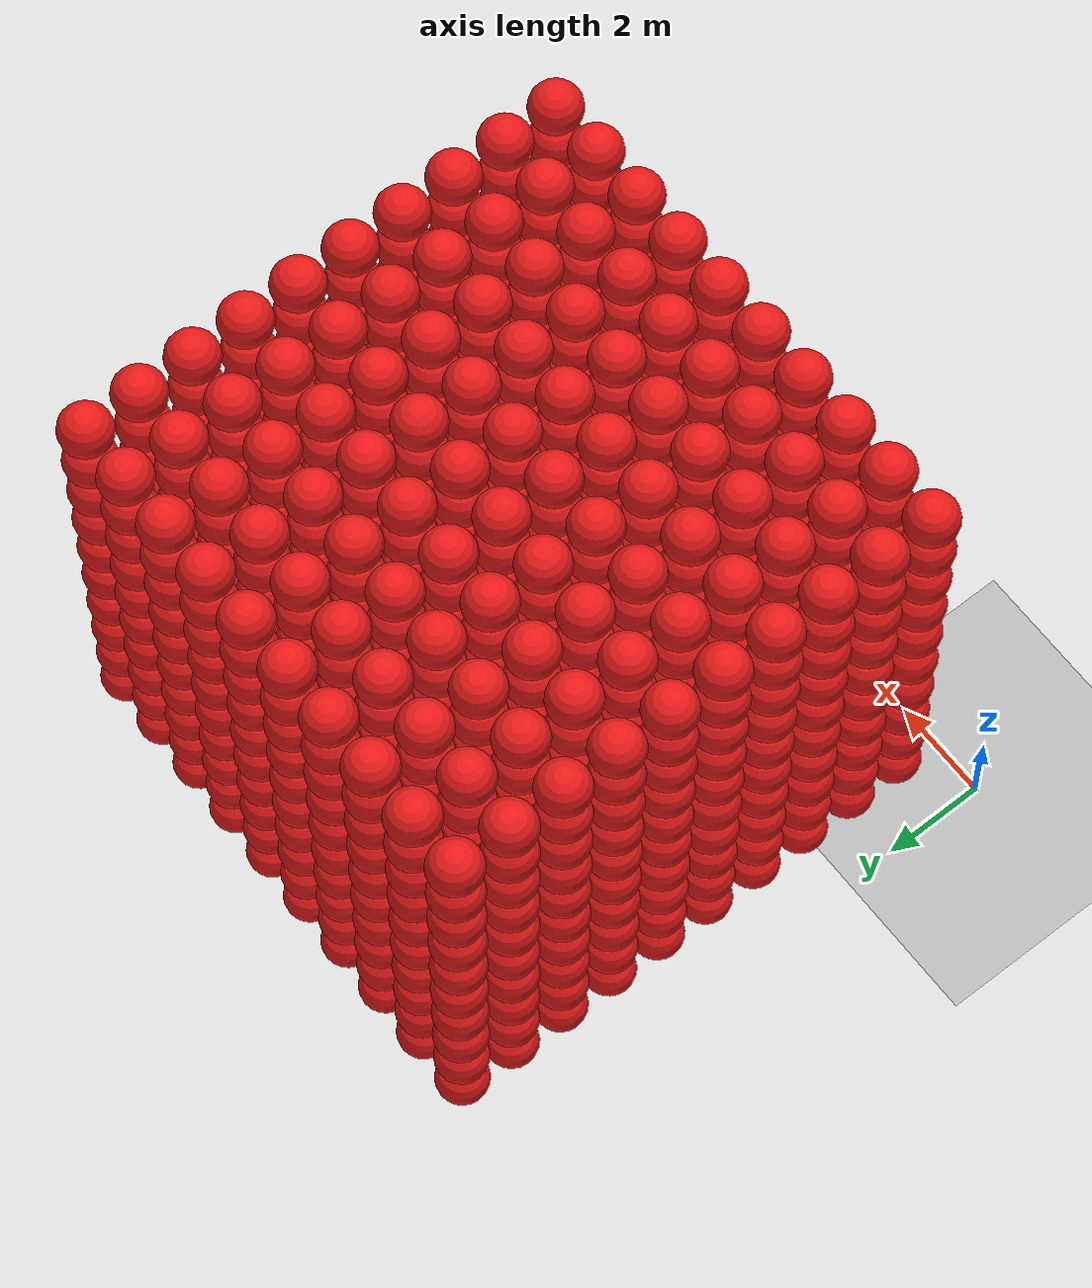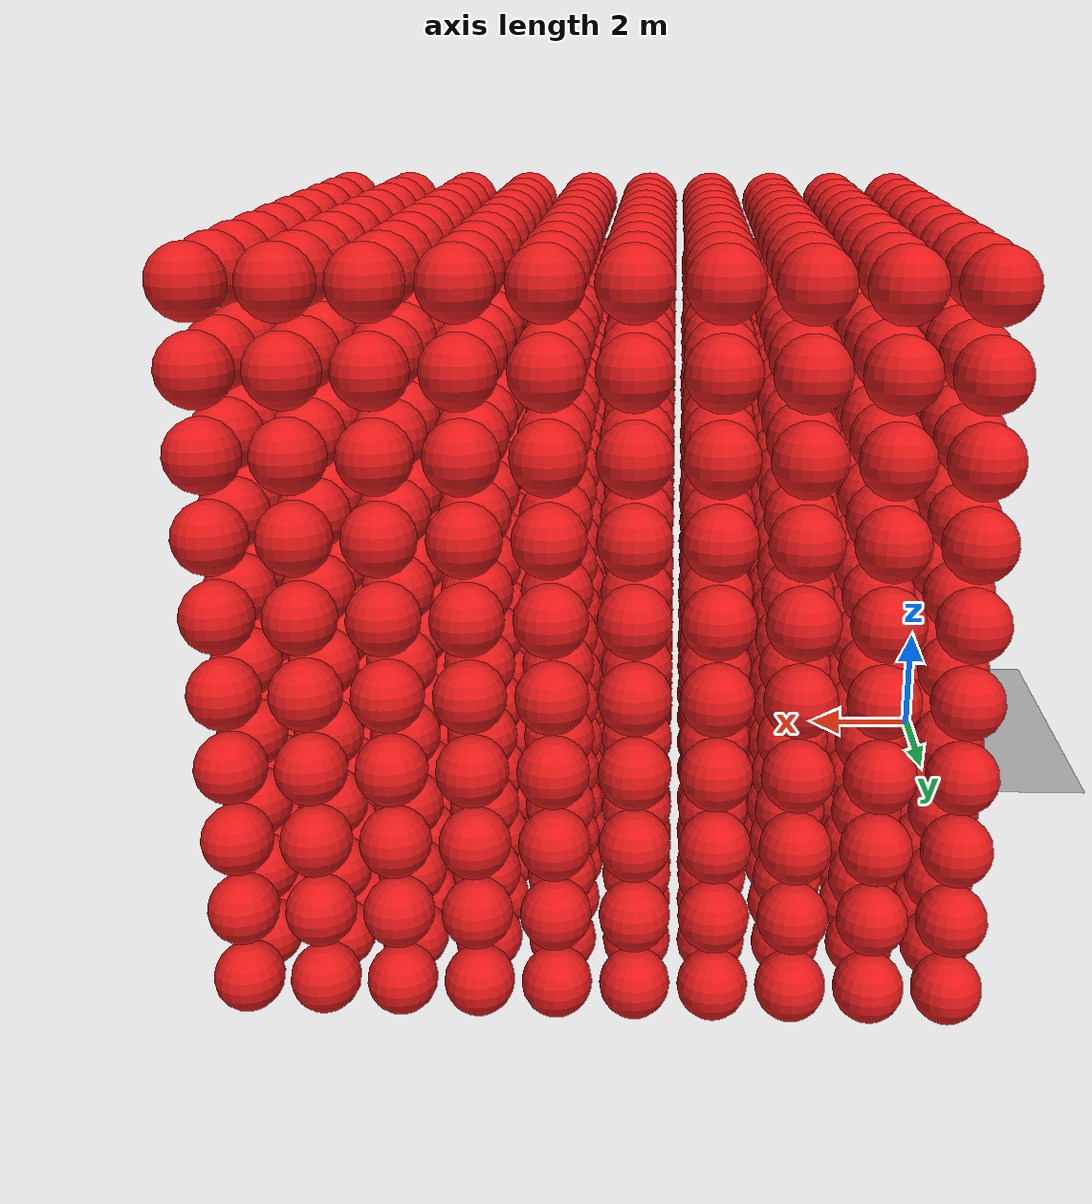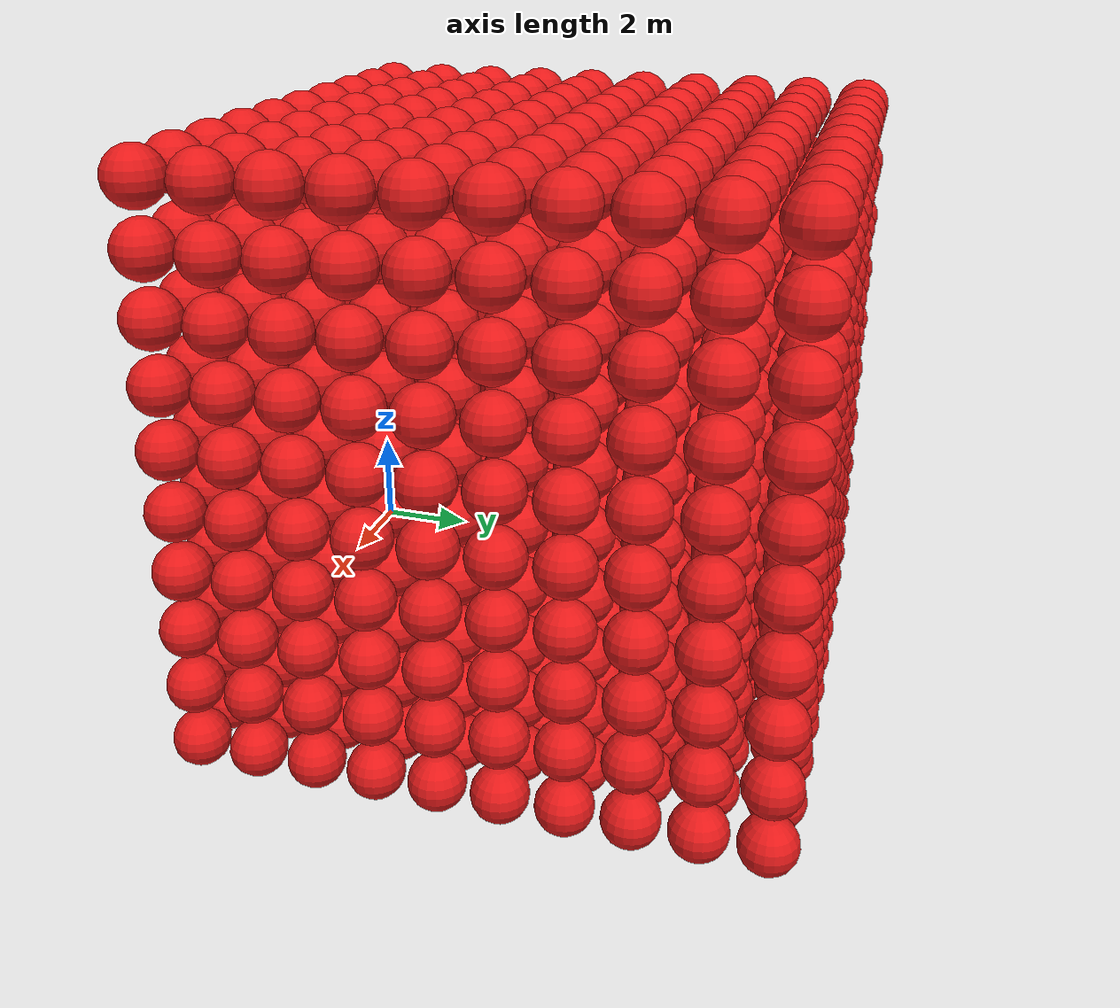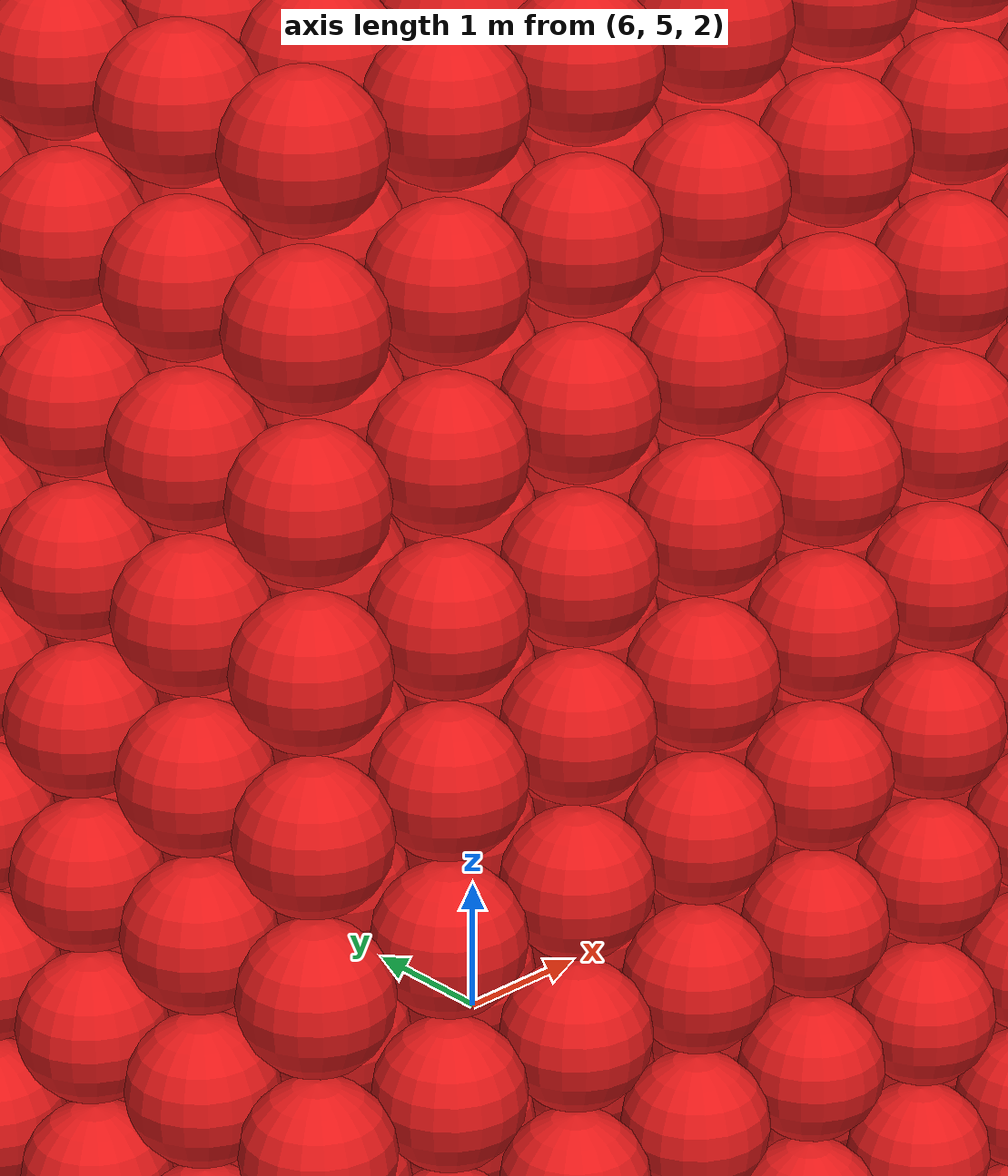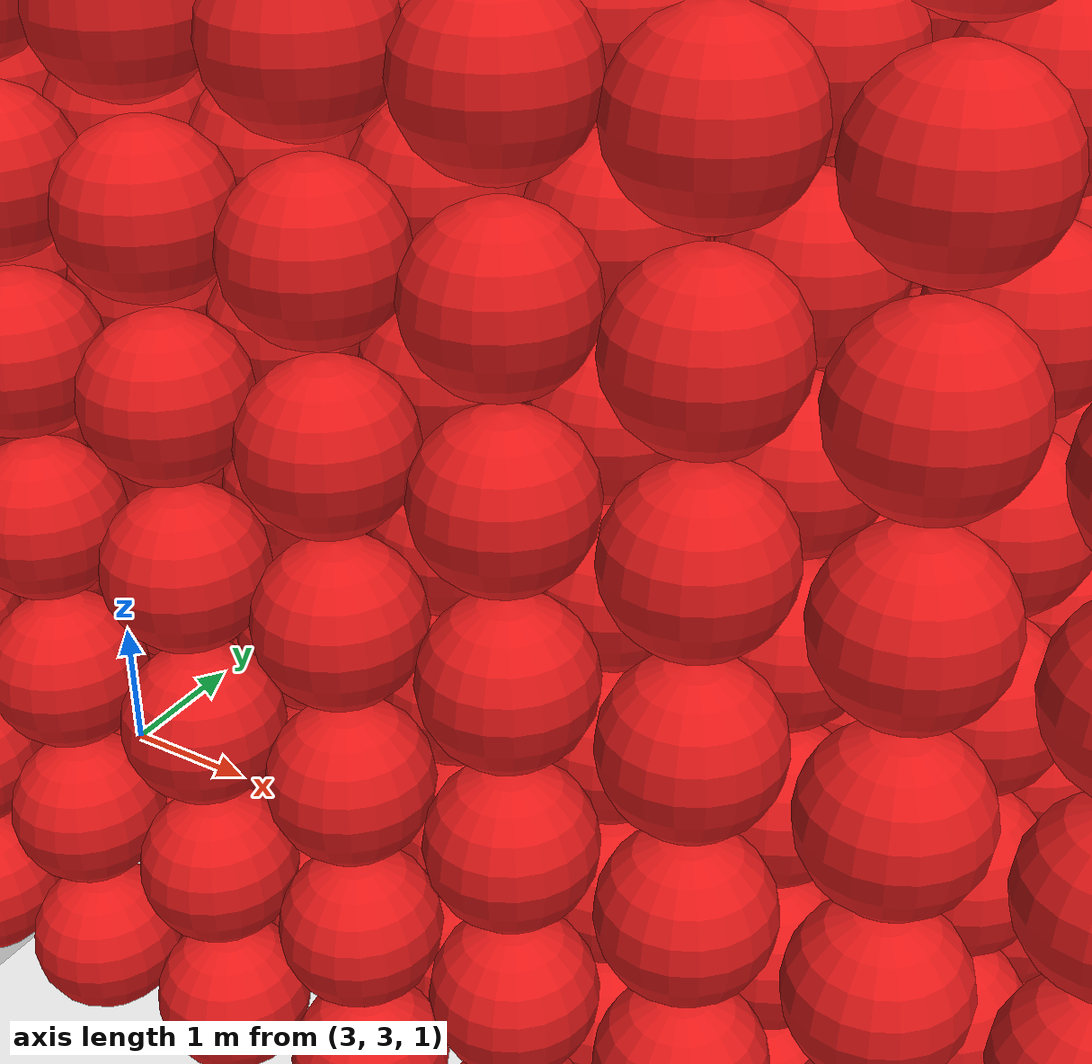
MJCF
<mujoco model="Humanoid and 100 objects">
    <compiler angle="degree"/>

    <option timestep="0.003" iterations="50" solver="PGS" jacobian="sparse" cone="elliptic" tolerance="1e-10"/>

    <size njmax="5000" nconmax="2000" nstack="1000000000"/>

    <default>
        <geom solimp=".9 .9 .01"/>

        <default class="object5">
            <geom type="sphere" material="geom" rgba=".9 .1 .1 1" size="0.5"/>
        </default>
    </default>

    <asset>
        <texture type="skybox" builtin="gradient" width="128" height="128" rgb1=".4 .6 .8" rgb2="0 0 0"/>
        <texture name="texgeom" type="cube" builtin="flat" mark="cross" width="128" height="128"
            rgb1="0.6 0.6 0.6" rgb2="0.6 0.6 0.6" markrgb="1 1 1"/>
        <texture name="texplane" type="2d" builtin="checker" rgb1=".4 .4 .4" rgb2=".6 .6 .6"
            width="512" height="512"/>
        <material name='geom' texture="texgeom" texuniform="true"/>
        <material name='MatPlane' reflectance='0.3' texture="texplane" texrepeat="1 1" texuniform="true"/>
    </asset>

    <visual>
        <quality shadowsize="4096" offsamples="8"/>
        <map znear="0.1" force="0.05"/>
    </visual>

    <statistic extent="4"/>

    <worldbody>
        <light directional="true" diffuse=".8 .8 .8" pos="0 0 10" dir="0 0 -10"/>

        <geom pos="0 0 0" type="plane" size="3 3 .5" rgba=".7 .7 .7 1" material="MatPlane"/>
<body pos="1.100930 1.100447 1.100834" quat="1 0 0 0"> <freejoint/> <geom class="object5"/> </body><body pos="1.100988 1.100370 2.200171" quat="1 0 0 0"> <freejoint/> <geom class="object5"/> </body><body pos="1.100823 1.100587 3.300962" quat="1 0 0 0"> <freejoint/> <geom class="object5"/> </body><body pos="1.100489 1.100254 4.400678" quat="1 0 0 0"> <freejoint/> <geom class="object5"/> </body><body pos="1.100914 1.100617 5.500322" quat="1 0 0 0"> <freejoint/> <geom class="object5"/> </body><body pos="1.100491 1.100407 6.600084" quat="1 0 0 0"> <freejoint/> <geom class="object5"/> </body><body pos="1.100592 1.100879 7.700553" quat="1 0 0 0"> <freejoint/> <geom class="object5"/> </body><body pos="1.100299 1.100897 8.800794" quat="1 0 0 0"> <freejoint/> <geom class="object5"/> </body><body pos="1.100776 1.100599 9.900557" quat="1 0 0 0"> <freejoint/> <geom class="object5"/> </body><body pos="1.100300 1.100548 11.000992" quat="1 0 0 0"> <freejoint/> <geom class="object5"/> </body><body pos="1.100483 2.200685 1.100480" quat="1 0 0 0"> <freejoint/> <geom class="object5"/> </body><body pos="1.100747 2.200211 2.200248" quat="1 0 0 0"> <freejoint/> <geom class="object5"/> </body><body pos="1.100098 2.200709 3.300856" quat="1 0 0 0"> <freejoint/> <geom class="object5"/> </body><body pos="1.100789 2.200743 4.400105" quat="1 0 0 0"> <freejoint/> <geom class="object5"/> </body><body pos="1.100521 2.200847 5.500844" quat="1 0 0 0"> <freejoint/> <geom class="object5"/> </body><body pos="1.100378 2.200272 6.600125" quat="1 0 0 0"> <freejoint/> <geom class="object5"/> </body><body pos="1.100691 2.200555 7.700008" quat="1 0 0 0"> <freejoint/> <geom class="object5"/> </body><body pos="1.100416 2.200439 8.800784" quat="1 0 0 0"> <freejoint/> <geom class="object5"/> </body><body pos="1.100830 2.200590 9.900142" quat="1 0 0 0"> <freejoint/> <geom class="object5"/> </body><body pos="1.100593 2.200726 11.000428" quat="1 0 0 0"> <freejoint/> <geom class="object5"/> </body><body pos="1.100211 3.300265 1.100993" quat="1 0 0 0"> <freejoint/> <geom class="object5"/> </body><body pos="1.100481 3.300828 2.200603" quat="1 0 0 0"> <freejoint/> <geom class="object5"/> </body><body pos="1.100818 3.300956 3.300650" quat="1 0 0 0"> <freejoint/> <geom class="object5"/> </body><body pos="1.100628 3.300647 4.400062" quat="1 0 0 0"> <freejoint/> <geom class="object5"/> </body><body pos="1.100938 3.300899 5.500695" quat="1 0 0 0"> <freejoint/> <geom class="object5"/> </body><body pos="1.100310 3.300344 6.600076" quat="1 0 0 0"> <freejoint/> <geom class="object5"/> </body><body pos="1.100520 3.300609 7.700727" quat="1 0 0 0"> <freejoint/> <geom class="object5"/> </body><body pos="1.100000 3.300170 8.800463" quat="1 0 0 0"> <freejoint/> <geom class="object5"/> </body><body pos="1.100362 3.300952 9.900932" quat="1 0 0 0"> <freejoint/> <geom class="object5"/> </body><body pos="1.100958 3.300207 11.000160" quat="1 0 0 0"> <freejoint/> <geom class="object5"/> </body><body pos="1.100572 4.400593 1.100699" quat="1 0 0 0"> <freejoint/> <geom class="object5"/> </body><body pos="1.100306 4.400394 2.200337" quat="1 0 0 0"> <freejoint/> <geom class="object5"/> </body><body pos="1.100129 4.400087 3.300549" quat="1 0 0 0"> <freejoint/> <geom class="object5"/> </body><body pos="1.100318 4.400993 4.400724" quat="1 0 0 0"> <freejoint/> <geom class="object5"/> </body><body pos="1.100572 4.400717 5.500977" quat="1 0 0 0"> <freejoint/> <geom class="object5"/> </body><body pos="1.100427 4.400913 6.600897" quat="1 0 0 0"> <freejoint/> <geom class="object5"/> </body><body pos="1.100835 4.400048 7.700359" quat="1 0 0 0"> <freejoint/> <geom class="object5"/> </body><body pos="1.100296 4.400629 8.800136" quat="1 0 0 0"> <freejoint/> <geom class="object5"/> </body><body pos="1.100374 4.400865 9.900250" quat="1 0 0 0"> <freejoint/> <geom class="object5"/> </body><body pos="1.100030 4.400999 11.000605" quat="1 0 0 0"> <freejoint/> <geom class="object5"/> </body><body pos="1.100244 5.500438 1.100735" quat="1 0 0 0"> <freejoint/> <geom class="object5"/> </body><body pos="1.100558 5.500438 2.200604" quat="1 0 0 0"> <freejoint/> <geom class="object5"/> </body><body pos="1.100181 5.500809 3.300819" quat="1 0 0 0"> <freejoint/> <geom class="object5"/> </body><body pos="1.100487 5.500755 4.400404" quat="1 0 0 0"> <freejoint/> <geom class="object5"/> </body><body pos="1.100726 5.500154 5.500509" quat="1 0 0 0"> <freejoint/> <geom class="object5"/> </body><body pos="1.100668 5.500153 6.600063" quat="1 0 0 0"> <freejoint/> <geom class="object5"/> </body><body pos="1.100337 5.500446 7.700758" quat="1 0 0 0"> <freejoint/> <geom class="object5"/> </body><body pos="1.100131 5.500902 8.800220" quat="1 0 0 0"> <freejoint/> <geom class="object5"/> </body><body pos="1.100379 5.500423 9.900973" quat="1 0 0 0"> <freejoint/> <geom class="object5"/> </body><body pos="1.100177 5.500882 11.000551" quat="1 0 0 0"> <freejoint/> <geom class="object5"/> </body><body pos="1.100321 6.600900 1.100542" quat="1 0 0 0"> <freejoint/> <geom class="object5"/> </body><body pos="1.100463 6.600808 2.200361" quat="1 0 0 0"> <freejoint/> <geom class="object5"/> </body><body pos="1.100971 6.600556 3.300770" quat="1 0 0 0"> <freejoint/> <geom class="object5"/> </body><body pos="1.100680 6.600205 4.400835" quat="1 0 0 0"> <freejoint/> <geom class="object5"/> </body><body pos="1.100865 6.600042 5.500614" quat="1 0 0 0"> <freejoint/> <geom class="object5"/> </body><body pos="1.100273 6.600747 6.600488" quat="1 0 0 0"> <freejoint/> <geom class="object5"/> </body><body pos="1.100792 6.600524 7.700598" quat="1 0 0 0"> <freejoint/> <geom class="object5"/> </body><body pos="1.100220 6.600364 8.800297" quat="1 0 0 0"> <freejoint/> <geom class="object5"/> </body><body pos="1.100852 6.600974 9.900624" quat="1 0 0 0"> <freejoint/> <geom class="object5"/> </body><body pos="1.100892 6.600981 11.000647" quat="1 0 0 0"> <freejoint/> <geom class="object5"/> </body><body pos="1.100799 7.700405 1.100482" quat="1 0 0 0"> <freejoint/> <geom class="object5"/> </body><body pos="1.100064 7.700803 2.200351" quat="1 0 0 0"> <freejoint/> <geom class="object5"/> </body><body pos="1.100849 7.700992 3.300484" quat="1 0 0 0"> <freejoint/> <geom class="object5"/> </body><body pos="1.100356 7.700054 4.400914" quat="1 0 0 0"> <freejoint/> <geom class="object5"/> </body><body pos="1.100705 7.700438 5.500968" quat="1 0 0 0"> <freejoint/> <geom class="object5"/> </body><body pos="1.100724 7.700657 6.600515" quat="1 0 0 0"> <freejoint/> <geom class="object5"/> </body><body pos="1.100877 7.700060 7.700471" quat="1 0 0 0"> <freejoint/> <geom class="object5"/> </body><body pos="1.100311 7.700195 8.800151" quat="1 0 0 0"> <freejoint/> <geom class="object5"/> </body><body pos="1.100901 7.700071 9.900958" quat="1 0 0 0"> <freejoint/> <geom class="object5"/> </body><body pos="1.100700 7.700012 11.000005" quat="1 0 0 0"> <freejoint/> <geom class="object5"/> </body><body pos="1.100853 8.800467 1.100837" quat="1 0 0 0"> <freejoint/> <geom class="object5"/> </body><body pos="1.100221 8.800806 2.200249" quat="1 0 0 0"> <freejoint/> <geom class="object5"/> </body><body pos="1.100998 8.800938 3.300554" quat="1 0 0 0"> <freejoint/> <geom class="object5"/> </body><body pos="1.100913 8.800635 4.400780" quat="1 0 0 0"> <freejoint/> <geom class="object5"/> </body><body pos="1.100567 8.800192 5.500906" quat="1 0 0 0"> <freejoint/> <geom class="object5"/> </body><body pos="1.100515 8.800999 6.600377" quat="1 0 0 0"> <freejoint/> <geom class="object5"/> </body><body pos="1.100206 8.800730 7.700313" quat="1 0 0 0"> <freejoint/> <geom class="object5"/> </body><body pos="1.100118 8.800889 8.800693" quat="1 0 0 0"> <freejoint/> <geom class="object5"/> </body><body pos="1.100940 8.800417 9.900816" quat="1 0 0 0"> <freejoint/> <geom class="object5"/> </body><body pos="1.100805 8.800360 11.000914" quat="1 0 0 0"> <freejoint/> <geom class="object5"/> </body><body pos="1.100288 9.900165 1.100456" quat="1 0 0 0"> <freejoint/> <geom class="object5"/> </body><body pos="1.100243 9.900002 2.200615" quat="1 0 0 0"> <freejoint/> <geom class="object5"/> </body><body pos="1.100661 9.900660 3.300680" quat="1 0 0 0"> <freejoint/> <geom class="object5"/> </body><body pos="1.100851 9.900037 4.400681" quat="1 0 0 0"> <freejoint/> <geom class="object5"/> </body><body pos="1.100571 9.900690 5.500896" quat="1 0 0 0"> <freejoint/> <geom class="object5"/> </body><body pos="1.100267 9.900069 6.600314" quat="1 0 0 0"> <freejoint/> <geom class="object5"/> </body><body pos="1.100789 9.900498 7.700437" quat="1 0 0 0"> <freejoint/> <geom class="object5"/> </body><body pos="1.100168 9.900265 8.800684" quat="1 0 0 0"> <freejoint/> <geom class="object5"/> </body><body pos="1.100817 9.900706 9.900577" quat="1 0 0 0"> <freejoint/> <geom class="object5"/> </body><body pos="1.100994 9.900461 11.000493" quat="1 0 0 0"> <freejoint/> <geom class="object5"/> </body><body pos="1.100274 11.000655 1.100407" quat="1 0 0 0"> <freejoint/> <geom class="object5"/> </body><body pos="1.100300 11.000605 2.200791" quat="1 0 0 0"> <freejoint/> <geom class="object5"/> </body><body pos="1.100971 11.000773 3.300600" quat="1 0 0 0"> <freejoint/> <geom class="object5"/> </body><body pos="1.100449 11.000153 4.400211" quat="1 0 0 0"> <freejoint/> <geom class="object5"/> </body><body pos="1.100700 11.000956 5.500635" quat="1 0 0 0"> <freejoint/> <geom class="object5"/> </body><body pos="1.100891 11.000216 6.600684" quat="1 0 0 0"> <freejoint/> <geom class="object5"/> </body><body pos="1.100315 11.000025 7.700820" quat="1 0 0 0"> <freejoint/> <geom class="object5"/> </body><body pos="1.100433 11.000089 8.800935" quat="1 0 0 0"> <freejoint/> <geom class="object5"/> </body><body pos="1.100391 11.000588 9.900240" quat="1 0 0 0"> <freejoint/> <geom class="object5"/> </body><body pos="1.100654 11.000367 11.000481" quat="1 0 0 0"> <freejoint/> <geom class="object5"/> </body><body pos="2.200402 1.100334 1.100268" quat="1 0 0 0"> <freejoint/> <geom class="object5"/> </body><body pos="2.200768 1.100240 2.200961" quat="1 0 0 0"> <freejoint/> <geom class="object5"/> </body><body pos="2.200924 1.100274 3.300223" quat="1 0 0 0"> <freejoint/> <geom class="object5"/> </body><body pos="2.200252 1.100247 4.400240" quat="1 0 0 0"> <freejoint/> <geom class="object5"/> </body><body pos="2.200428 1.100826 5.500617" quat="1 0 0 0"> <freejoint/> <geom class="object5"/> </body><body pos="2.200194 1.100808 6.600986" quat="1 0 0 0"> <freejoint/> <geom class="object5"/> </body><body pos="2.200149 1.100853 7.700239" quat="1 0 0 0"> <freejoint/> <geom class="object5"/> </body><body pos="2.200417 1.100322 8.800434" quat="1 0 0 0"> <freejoint/> <geom class="object5"/> </body><body pos="2.200327 1.100099 9.900671" quat="1 0 0 0"> <freejoint/> <geom class="object5"/> </body><body pos="2.200049 1.100201 11.000499" quat="1 0 0 0"> <freejoint/> <geom class="object5"/> </body><body pos="2.200275 2.200420 1.100597" quat="1 0 0 0"> <freejoint/> <geom class="object5"/> </body><body pos="2.200049 2.200887 2.200858" quat="1 0 0 0"> <freejoint/> <geom class="object5"/> </body><body pos="2.200085 2.200177 3.300013" quat="1 0 0 0"> <freejoint/> <geom class="object5"/> </body><body pos="2.200590 2.200708 4.400759" quat="1 0 0 0"> <freejoint/> <geom class="object5"/> </body><body pos="2.200214 2.200966 5.500484" quat="1 0 0 0"> <freejoint/> <geom class="object5"/> </body><body pos="2.200062 2.200178 6.600338" quat="1 0 0 0"> <freejoint/> <geom class="object5"/> </body><body pos="2.200880 2.200043 7.700355" quat="1 0 0 0"> <freejoint/> <geom class="object5"/> </body><body pos="2.200641 2.200828 8.800045" quat="1 0 0 0"> <freejoint/> <geom class="object5"/> </body><body pos="2.200791 2.200051 9.900296" quat="1 0 0 0"> <freejoint/> <geom class="object5"/> </body><body pos="2.200272 2.200913 11.000605" quat="1 0 0 0"> <freejoint/> <geom class="object5"/> </body><body pos="2.200502 3.300737 1.100112" quat="1 0 0 0"> <freejoint/> <geom class="object5"/> </body><body pos="2.200884 3.300530 2.200005" quat="1 0 0 0"> <freejoint/> <geom class="object5"/> </body><body pos="2.200163 3.300262 3.300039" quat="1 0 0 0"> <freejoint/> <geom class="object5"/> </body><body pos="2.200682 3.300028 4.400500" quat="1 0 0 0"> <freejoint/> <geom class="object5"/> </body><body pos="2.200481 3.300279 5.500590" quat="1 0 0 0"> <freejoint/> <geom class="object5"/> </body><body pos="2.200287 3.300920 6.600006" quat="1 0 0 0"> <freejoint/> <geom class="object5"/> </body><body pos="2.200565 3.300369 7.700371" quat="1 0 0 0"> <freejoint/> <geom class="object5"/> </body><body pos="2.200021 3.300687 8.800555" quat="1 0 0 0"> <freejoint/> <geom class="object5"/> </body><body pos="2.200765 3.300791 9.900247" quat="1 0 0 0"> <freejoint/> <geom class="object5"/> </body><body pos="2.200200 3.300367 11.000720" quat="1 0 0 0"> <freejoint/> <geom class="object5"/> </body><body pos="2.200125 4.400430 1.100016" quat="1 0 0 0"> <freejoint/> <geom class="object5"/> </body><body pos="2.200071 4.400710 2.200803" quat="1 0 0 0"> <freejoint/> <geom class="object5"/> </body><body pos="2.200910 4.400912 3.300630" quat="1 0 0 0"> <freejoint/> <geom class="object5"/> </body><body pos="2.200131 4.400062 4.400778" quat="1 0 0 0"> <freejoint/> <geom class="object5"/> </body><body pos="2.200742 4.400626 5.500729" quat="1 0 0 0"> <freejoint/> <geom class="object5"/> </body><body pos="2.200203 4.400795 6.600975" quat="1 0 0 0"> <freejoint/> <geom class="object5"/> </body><body pos="2.200420 4.400246 7.700480" quat="1 0 0 0"> <freejoint/> <geom class="object5"/> </body><body pos="2.200669 4.400852 8.800945" quat="1 0 0 0"> <freejoint/> <geom class="object5"/> </body><body pos="2.200129 4.400697 9.900080" quat="1 0 0 0"> <freejoint/> <geom class="object5"/> </body><body pos="2.200104 4.400131 11.000515" quat="1 0 0 0"> <freejoint/> <geom class="object5"/> </body><body pos="2.200482 5.500446 1.100798" quat="1 0 0 0"> <freejoint/> <geom class="object5"/> </body><body pos="2.200529 5.500669 2.200483" quat="1 0 0 0"> <freejoint/> <geom class="object5"/> </body><body pos="2.200333 5.500259 3.300974" quat="1 0 0 0"> <freejoint/> <geom class="object5"/> </body><body pos="2.200264 5.500790 4.400497" quat="1 0 0 0"> <freejoint/> <geom class="object5"/> </body><body pos="2.200321 5.500616 5.500007" quat="1 0 0 0"> <freejoint/> <geom class="object5"/> </body><body pos="2.200063 5.500920 6.600906" quat="1 0 0 0"> <freejoint/> <geom class="object5"/> </body><body pos="2.200832 5.500914 7.700679" quat="1 0 0 0"> <freejoint/> <geom class="object5"/> </body><body pos="2.200777 5.500694 8.800199" quat="1 0 0 0"> <freejoint/> <geom class="object5"/> </body><body pos="2.200452 5.500789 9.900002" quat="1 0 0 0"> <freejoint/> <geom class="object5"/> </body><body pos="2.200556 5.500433 11.000058" quat="1 0 0 0"> <freejoint/> <geom class="object5"/> </body><body pos="2.200442 6.600840 1.100618" quat="1 0 0 0"> <freejoint/> <geom class="object5"/> </body><body pos="2.200742 6.600936 2.200325" quat="1 0 0 0"> <freejoint/> <geom class="object5"/> </body><body pos="2.200746 6.600873 3.300433" quat="1 0 0 0"> <freejoint/> <geom class="object5"/> </body><body pos="2.200522 6.600653 4.400469" quat="1 0 0 0"> <freejoint/> <geom class="object5"/> </body><body pos="2.200183 6.600226 5.500412" quat="1 0 0 0"> <freejoint/> <geom class="object5"/> </body><body pos="2.200015 6.600751 6.600062" quat="1 0 0 0"> <freejoint/> <geom class="object5"/> </body><body pos="2.200432 6.600543 7.700610" quat="1 0 0 0"> <freejoint/> <geom class="object5"/> </body><body pos="2.200436 6.600081 8.800284" quat="1 0 0 0"> <freejoint/> <geom class="object5"/> </body><body pos="2.200073 6.600730 9.900346" quat="1 0 0 0"> <freejoint/> <geom class="object5"/> </body><body pos="2.200652 6.600482 11.000383" quat="1 0 0 0"> <freejoint/> <geom class="object5"/> </body><body pos="2.200327 7.700103 1.100370" quat="1 0 0 0"> <freejoint/> <geom class="object5"/> </body><body pos="2.200377 7.700482 2.200796" quat="1 0 0 0"> <freejoint/> <geom class="object5"/> </body><body pos="2.200691 7.700850 3.300512" quat="1 0 0 0"> <freejoint/> <geom class="object5"/> </body><body pos="2.200855 7.700465 4.400265" quat="1 0 0 0"> <freejoint/> <geom class="object5"/> </body><body pos="2.200629 7.700563 5.500541" quat="1 0 0 0"> <freejoint/> <geom class="object5"/> </body><body pos="2.200393 7.700420 6.600137" quat="1 0 0 0"> <freejoint/> <geom class="object5"/> </body><body pos="2.200292 7.700007 7.700933" quat="1 0 0 0"> <freejoint/> <geom class="object5"/> </body><body pos="2.200609 7.700892 8.800421" quat="1 0 0 0"> <freejoint/> <geom class="object5"/> </body><body pos="2.200400 7.700554 9.900596" quat="1 0 0 0"> <freejoint/> <geom class="object5"/> </body><body pos="2.200506 7.700587 11.000133" quat="1 0 0 0"> <freejoint/> <geom class="object5"/> </body><body pos="2.200762 8.800651 1.100351" quat="1 0 0 0"> <freejoint/> <geom class="object5"/> </body><body pos="2.200313 8.800274 2.200150" quat="1 0 0 0"> <freejoint/> <geom class="object5"/> </body><body pos="2.200334 8.800833 3.300234" quat="1 0 0 0"> <freejoint/> <geom class="object5"/> </body><body pos="2.200069 8.800495 4.400122" quat="1 0 0 0"> <freejoint/> <geom class="object5"/> </body><body pos="2.200403 8.800091 5.500721" quat="1 0 0 0"> <freejoint/> <geom class="object5"/> </body><body pos="2.200342 8.800566 6.600655" quat="1 0 0 0"> <freejoint/> <geom class="object5"/> </body><body pos="2.200653 8.800701 7.700301" quat="1 0 0 0"> <freejoint/> <geom class="object5"/> </body><body pos="2.200085 8.800633 8.800266" quat="1 0 0 0"> <freejoint/> <geom class="object5"/> </body><body pos="2.200894 8.800300 9.900715" quat="1 0 0 0"> <freejoint/> <geom class="object5"/> </body><body pos="2.200330 8.800365 11.000592" quat="1 0 0 0"> <freejoint/> <geom class="object5"/> </body><body pos="2.200905 9.900265 1.100950" quat="1 0 0 0"> <freejoint/> <geom class="object5"/> </body><body pos="2.200739 9.900004 2.200851" quat="1 0 0 0"> <freejoint/> <geom class="object5"/> </body><body pos="2.200696 9.900562 3.300338" quat="1 0 0 0"> <freejoint/> <geom class="object5"/> </body><body pos="2.200333 9.900077 4.400458" quat="1 0 0 0"> <freejoint/> <geom class="object5"/> </body><body pos="2.200657 9.900572 5.500402" quat="1 0 0 0"> <freejoint/> <geom class="object5"/> </body><body pos="2.200935 9.900361 6.600948" quat="1 0 0 0"> <freejoint/> <geom class="object5"/> </body><body pos="2.200030 9.900441 7.700701" quat="1 0 0 0"> <freejoint/> <geom class="object5"/> </body><body pos="2.200703 9.900510 8.800612" quat="1 0 0 0"> <freejoint/> <geom class="object5"/> </body><body pos="2.200746 9.900801 9.900337" quat="1 0 0 0"> <freejoint/> <geom class="object5"/> </body><body pos="2.200564 9.900855 11.000589" quat="1 0 0 0"> <freejoint/> <geom class="object5"/> </body><body pos="2.200508 11.000853 1.100684" quat="1 0 0 0"> <freejoint/> <geom class="object5"/> </body><body pos="2.200106 11.000502 2.200019" quat="1 0 0 0"> <freejoint/> <geom class="object5"/> </body><body pos="2.200443 11.000907 3.300045" quat="1 0 0 0"> <freejoint/> <geom class="object5"/> </body><body pos="2.200945 11.000180 4.400370" quat="1 0 0 0"> <freejoint/> <geom class="object5"/> </body><body pos="2.200205 11.000096 5.500433" quat="1 0 0 0"> <freejoint/> <geom class="object5"/> </body><body pos="2.200278 11.000101 6.600499" quat="1 0 0 0"> <freejoint/> <geom class="object5"/> </body><body pos="2.200239 11.000350 7.700558" quat="1 0 0 0"> <freejoint/> <geom class="object5"/> </body><body pos="2.200548 11.000421 8.800385" quat="1 0 0 0"> <freejoint/> <geom class="object5"/> </body><body pos="2.200381 11.000281 9.900180" quat="1 0 0 0"> <freejoint/> <geom class="object5"/> </body><body pos="2.200127 11.000016 11.000753" quat="1 0 0 0"> <freejoint/> <geom class="object5"/> </body><body pos="3.300505 1.100722 1.100761" quat="1 0 0 0"> <freejoint/> <geom class="object5"/> </body><body pos="3.300269 1.100194 2.200064" quat="1 0 0 0"> <freejoint/> <geom class="object5"/> </body><body pos="3.300425 1.100702 3.300977" quat="1 0 0 0"> <freejoint/> <geom class="object5"/> </body><body pos="3.300552 1.100044 4.400582" quat="1 0 0 0"> <freejoint/> <geom class="object5"/> </body><body pos="3.300278 1.100542 5.500443" quat="1 0 0 0"> <freejoint/> <geom class="object5"/> </body><body pos="3.300117 1.100380 6.600765" quat="1 0 0 0"> <freejoint/> <geom class="object5"/> </body><body pos="3.300918 1.100693 7.700971" quat="1 0 0 0"> <freejoint/> <geom class="object5"/> </body><body pos="3.300126 1.100646 8.800387" quat="1 0 0 0"> <freejoint/> <geom class="object5"/> </body><body pos="3.300562 1.100198 9.900394" quat="1 0 0 0"> <freejoint/> <geom class="object5"/> </body><body pos="3.300340 1.100356 11.000373" quat="1 0 0 0"> <freejoint/> <geom class="object5"/> </body><body pos="3.300115 2.200501 1.100817" quat="1 0 0 0"> <freejoint/> <geom class="object5"/> </body><body pos="3.300344 2.200499 2.200118" quat="1 0 0 0"> <freejoint/> <geom class="object5"/> </body><body pos="3.300576 2.200515 3.300355" quat="1 0 0 0"> <freejoint/> <geom class="object5"/> </body><body pos="3.300863 2.200344 4.400457" quat="1 0 0 0"> <freejoint/> <geom class="object5"/> </body><body pos="3.300238 2.200771 5.500273" quat="1 0 0 0"> <freejoint/> <geom class="object5"/> </body><body pos="3.300525 2.200531 6.600873" quat="1 0 0 0"> <freejoint/> <geom class="object5"/> </body><body pos="3.300938 2.200049 7.700979" quat="1 0 0 0"> <freejoint/> <geom class="object5"/> </body><body pos="3.300632 2.200073 8.800212" quat="1 0 0 0"> <freejoint/> <geom class="object5"/> </body><body pos="3.300360 2.200427 9.900758" quat="1 0 0 0"> <freejoint/> <geom class="object5"/> </body><body pos="3.300916 2.200630 11.000956" quat="1 0 0 0"> <freejoint/> <geom class="object5"/> </body><body pos="3.300755 3.300526 1.100850" quat="1 0 0 0"> <freejoint/> <geom class="object5"/> </body><body pos="3.300816 3.300132 2.200761" quat="1 0 0 0"> <freejoint/> <geom class="object5"/> </body><body pos="3.300617 3.300398 3.300841" quat="1 0 0 0"> <freejoint/> <geom class="object5"/> </body><body pos="3.300038 3.300096 4.400948" quat="1 0 0 0"> <freejoint/> <geom class="object5"/> </body><body pos="3.300396 3.300532 5.500904" quat="1 0 0 0"> <freejoint/> <geom class="object5"/> </body><body pos="3.300340 3.300664 6.600727" quat="1 0 0 0"> <freejoint/> <geom class="object5"/> </body><body pos="3.300223 3.300555 7.700455" quat="1 0 0 0"> <freejoint/> <geom class="object5"/> </body><body pos="3.300610 3.300544 8.800518" quat="1 0 0 0"> <freejoint/> <geom class="object5"/> </body><body pos="3.300286 3.300879 9.900937" quat="1 0 0 0"> <freejoint/> <geom class="object5"/> </body><body pos="3.300806 3.300969 11.000524" quat="1 0 0 0"> <freejoint/> <geom class="object5"/> </body><body pos="3.300113 4.400650 1.100191" quat="1 0 0 0"> <freejoint/> <geom class="object5"/> </body><body pos="3.300857 4.400943 2.200103" quat="1 0 0 0"> <freejoint/> <geom class="object5"/> </body><body pos="3.300296 4.400799 3.300442" quat="1 0 0 0"> <freejoint/> <geom class="object5"/> </body><body pos="3.300493 4.400030 4.400573" quat="1 0 0 0"> <freejoint/> <geom class="object5"/> </body><body pos="3.300572 4.400742 5.500077" quat="1 0 0 0"> <freejoint/> <geom class="object5"/> </body><body pos="3.300787 4.400193 6.600531" quat="1 0 0 0"> <freejoint/> <geom class="object5"/> </body><body pos="3.300924 4.400986 7.700975" quat="1 0 0 0"> <freejoint/> <geom class="object5"/> </body><body pos="3.300305 4.400754 8.800206" quat="1 0 0 0"> <freejoint/> <geom class="object5"/> </body><body pos="3.300861 4.400658 9.900102" quat="1 0 0 0"> <freejoint/> <geom class="object5"/> </body><body pos="3.300580 4.400963 11.000845" quat="1 0 0 0"> <freejoint/> <geom class="object5"/> </body><body pos="3.300753 5.500703 1.100247" quat="1 0 0 0"> <freejoint/> <geom class="object5"/> </body><body pos="3.300040 5.500462 2.200117" quat="1 0 0 0"> <freejoint/> <geom class="object5"/> </body><body pos="3.300162 5.500420 3.300666" quat="1 0 0 0"> <freejoint/> <geom class="object5"/> </body><body pos="3.300973 5.500280 4.400531" quat="1 0 0 0"> <freejoint/> <geom class="object5"/> </body><body pos="3.300931 5.500167 5.500789" quat="1 0 0 0"> <freejoint/> <geom class="object5"/> </body><body pos="3.300103 5.500884 6.600522" quat="1 0 0 0"> <freejoint/> <geom class="object5"/> </body><body pos="3.300974 5.500756 7.700723" quat="1 0 0 0"> <freejoint/> <geom class="object5"/> </body><body pos="3.300003 5.500206 8.800260" quat="1 0 0 0"> <freejoint/> <geom class="object5"/> </body><body pos="3.300080 5.500735 9.900823" quat="1 0 0 0"> <freejoint/> <geom class="object5"/> </body><body pos="3.300343 5.500136 11.000666" quat="1 0 0 0"> <freejoint/> <geom class="object5"/> </body><body pos="3.300830 6.600674 1.100139" quat="1 0 0 0"> <freejoint/> <geom class="object5"/> </body><body pos="3.300379 6.600678 2.200516" quat="1 0 0 0"> <freejoint/> <geom class="object5"/> </body><body pos="3.300978 6.600268 3.300867" quat="1 0 0 0"> <freejoint/> <geom class="object5"/> </body><body pos="3.300374 6.600137 4.400083" quat="1 0 0 0"> <freejoint/> <geom class="object5"/> </body><body pos="3.300739 6.600372 5.500381" quat="1 0 0 0"> <freejoint/> <geom class="object5"/> </body><body pos="3.300302 6.600295 6.600260" quat="1 0 0 0"> <freejoint/> <geom class="object5"/> </body><body pos="3.300463 6.600988 7.700385" quat="1 0 0 0"> <freejoint/> <geom class="object5"/> </body><body pos="3.300943 6.600167 8.800925" quat="1 0 0 0"> <freejoint/> <geom class="object5"/> </body><body pos="3.300754 6.600857 9.900602" quat="1 0 0 0"> <freejoint/> <geom class="object5"/> </body><body pos="3.300107 6.600455 11.000655" quat="1 0 0 0"> <freejoint/> <geom class="object5"/> </body><body pos="3.300058 7.700021 1.100290" quat="1 0 0 0"> <freejoint/> <geom class="object5"/> </body><body pos="3.300931 7.700514 2.200875" quat="1 0 0 0"> <freejoint/> <geom class="object5"/> </body><body pos="3.300378 7.700885 3.300535" quat="1 0 0 0"> <freejoint/> <geom class="object5"/> </body><body pos="3.300893 7.700103 4.400212" quat="1 0 0 0"> <freejoint/> <geom class="object5"/> </body><body pos="3.300702 7.700361 5.500001" quat="1 0 0 0"> <freejoint/> <geom class="object5"/> </body><body pos="3.300384 7.700320 6.600393" quat="1 0 0 0"> <freejoint/> <geom class="object5"/> </body><body pos="3.300181 7.700209 7.700594" quat="1 0 0 0"> <freejoint/> <geom class="object5"/> </body><body pos="3.300594 7.700172 8.800933" quat="1 0 0 0"> <freejoint/> <geom class="object5"/> </body><body pos="3.300056 7.700202 9.900508" quat="1 0 0 0"> <freejoint/> <geom class="object5"/> </body><body pos="3.300759 7.700146 11.000931" quat="1 0 0 0"> <freejoint/> <geom class="object5"/> </body><body pos="3.300422 8.800056 1.100674" quat="1 0 0 0"> <freejoint/> <geom class="object5"/> </body><body pos="3.300280 8.800780 2.200963" quat="1 0 0 0"> <freejoint/> <geom class="object5"/> </body><body pos="3.300688 8.800498 3.300099" quat="1 0 0 0"> <freejoint/> <geom class="object5"/> </body><body pos="3.300288 8.800538 4.400011" quat="1 0 0 0"> <freejoint/> <geom class="object5"/> </body><body pos="3.300283 8.800590 5.500172" quat="1 0 0 0"> <freejoint/> <geom class="object5"/> </body><body pos="3.300170 8.800676 6.600570" quat="1 0 0 0"> <freejoint/> <geom class="object5"/> </body><body pos="3.300552 8.800967 7.700628" quat="1 0 0 0"> <freejoint/> <geom class="object5"/> </body><body pos="3.300325 8.800521 8.800865" quat="1 0 0 0"> <freejoint/> <geom class="object5"/> </body><body pos="3.300994 8.800838 9.900347" quat="1 0 0 0"> <freejoint/> <geom class="object5"/> </body><body pos="3.300749 8.800939 11.000668" quat="1 0 0 0"> <freejoint/> <geom class="object5"/> </body><body pos="3.300481 9.900286 1.100595" quat="1 0 0 0"> <freejoint/> <geom class="object5"/> </body><body pos="3.300336 9.900960 2.200442" quat="1 0 0 0"> <freejoint/> <geom class="object5"/> </body><body pos="3.300962 9.900676 3.300706" quat="1 0 0 0"> <freejoint/> <geom class="object5"/> </body><body pos="3.300958 9.900940 4.400834" quat="1 0 0 0"> <freejoint/> <geom class="object5"/> </body><body pos="3.300155 9.900830 5.500464" quat="1 0 0 0"> <freejoint/> <geom class="object5"/> </body><body pos="3.300299 9.900523 6.600832" quat="1 0 0 0"> <freejoint/> <geom class="object5"/> </body><body pos="3.300539 9.900260 7.700354" quat="1 0 0 0"> <freejoint/> <geom class="object5"/> </body><body pos="3.300187 9.900351 8.800190" quat="1 0 0 0"> <freejoint/> <geom class="object5"/> </body><body pos="3.300836 9.900384 9.900009" quat="1 0 0 0"> <freejoint/> <geom class="object5"/> </body><body pos="3.300309 9.900837 11.000281" quat="1 0 0 0"> <freejoint/> <geom class="object5"/> </body><body pos="3.300781 11.000532 1.100154" quat="1 0 0 0"> <freejoint/> <geom class="object5"/> </body><body pos="3.300525 11.000283 2.200715" quat="1 0 0 0"> <freejoint/> <geom class="object5"/> </body><body pos="3.300734 11.000450 3.300182" quat="1 0 0 0"> <freejoint/> <geom class="object5"/> </body><body pos="3.300136 11.000273 4.400636" quat="1 0 0 0"> <freejoint/> <geom class="object5"/> </body><body pos="3.300806 11.000668 5.500287" quat="1 0 0 0"> <freejoint/> <geom class="object5"/> </body><body pos="3.300142 11.000246 6.600692" quat="1 0 0 0"> <freejoint/> <geom class="object5"/> </body><body pos="3.300072 11.000499 7.700986" quat="1 0 0 0"> <freejoint/> <geom class="object5"/> </body><body pos="3.300905 11.000575 8.800767" quat="1 0 0 0"> <freejoint/> <geom class="object5"/> </body><body pos="3.300747 11.000695 9.900677" quat="1 0 0 0"> <freejoint/> <geom class="object5"/> </body><body pos="3.300282 11.000582 11.000619" quat="1 0 0 0"> <freejoint/> <geom class="object5"/> </body><body pos="4.400814 1.100016 1.100214" quat="1 0 0 0"> <freejoint/> <geom class="object5"/> </body><body pos="4.400988 1.100817 2.200632" quat="1 0 0 0"> <freejoint/> <geom class="object5"/> </body><body pos="4.400682 1.100808 3.300280" quat="1 0 0 0"> <freejoint/> <geom class="object5"/> </body><body pos="4.400665 1.100029 4.400544" quat="1 0 0 0"> <freejoint/> <geom class="object5"/> </body><body pos="4.400529 1.100873 5.500188" quat="1 0 0 0"> <freejoint/> <geom class="object5"/> </body><body pos="4.400931 1.100976 6.600331" quat="1 0 0 0"> <freejoint/> <geom class="object5"/> </body><body pos="4.400624 1.100527 7.700459" quat="1 0 0 0"> <freejoint/> <geom class="object5"/> </body><body pos="4.400359 1.100334 8.800083" quat="1 0 0 0"> <freejoint/> <geom class="object5"/> </body><body pos="4.400390 1.100239 9.900486" quat="1 0 0 0"> <freejoint/> <geom class="object5"/> </body><body pos="4.400700 1.100137 11.000826" quat="1 0 0 0"> <freejoint/> <geom class="object5"/> </body><body pos="4.400930 2.200829 1.100485" quat="1 0 0 0"> <freejoint/> <geom class="object5"/> </body><body pos="4.400660 2.200456 2.200418" quat="1 0 0 0"> <freejoint/> <geom class="object5"/> </body><body pos="4.400034 2.200927 3.300043" quat="1 0 0 0"> <freejoint/> <geom class="object5"/> </body><body pos="4.400476 2.200386 4.400534" quat="1 0 0 0"> <freejoint/> <geom class="object5"/> </body><body pos="4.400998 2.200902 5.500015" quat="1 0 0 0"> <freejoint/> <geom class="object5"/> </body><body pos="4.400781 2.200485 6.600390" quat="1 0 0 0"> <freejoint/> <geom class="object5"/> </body><body pos="4.400823 2.200874 7.700998" quat="1 0 0 0"> <freejoint/> <geom class="object5"/> </body><body pos="4.400196 2.200870 8.800307" quat="1 0 0 0"> <freejoint/> <geom class="object5"/> </body><body pos="4.400411 2.200816 9.900368" quat="1 0 0 0"> <freejoint/> <geom class="object5"/> </body><body pos="4.400426 2.200091 11.000667" quat="1 0 0 0"> <freejoint/> <geom class="object5"/> </body><body pos="4.400731 3.300301 1.100338" quat="1 0 0 0"> <freejoint/> <geom class="object5"/> </body><body pos="4.400734 3.300985 2.200699" quat="1 0 0 0"> <freejoint/> <geom class="object5"/> </body><body pos="4.400090 3.300471 3.300635" quat="1 0 0 0"> <freejoint/> <geom class="object5"/> </body><body pos="4.400525 3.300141 4.400276" quat="1 0 0 0"> <freejoint/> <geom class="object5"/> </body><body pos="4.400987 3.300795 5.500933" quat="1 0 0 0"> <freejoint/> <geom class="object5"/> </body><body pos="4.400348 3.300209 6.600680" quat="1 0 0 0"> <freejoint/> <geom class="object5"/> </body><body pos="4.400355 3.300438 7.700909" quat="1 0 0 0"> <freejoint/> <geom class="object5"/> </body><body pos="4.400834 3.300391 8.800734" quat="1 0 0 0"> <freejoint/> <geom class="object5"/> </body><body pos="4.400291 3.300292 9.900297" quat="1 0 0 0"> <freejoint/> <geom class="object5"/> </body><body pos="4.400025 3.300918 11.000686" quat="1 0 0 0"> <freejoint/> <geom class="object5"/> </body><body pos="4.400234 4.400497 1.100791" quat="1 0 0 0"> <freejoint/> <geom class="object5"/> </body><body pos="4.400380 4.400219 2.200723" quat="1 0 0 0"> <freejoint/> <geom class="object5"/> </body><body pos="4.400773 4.400693 3.300620" quat="1 0 0 0"> <freejoint/> <geom class="object5"/> </body><body pos="4.400762 4.400511 4.400329" quat="1 0 0 0"> <freejoint/> <geom class="object5"/> </body><body pos="4.400001 4.400581 5.500172" quat="1 0 0 0"> <freejoint/> <geom class="object5"/> </body><body pos="4.400195 4.400150 6.600505" quat="1 0 0 0"> <freejoint/> <geom class="object5"/> </body><body pos="4.400017 4.400471 7.700046" quat="1 0 0 0"> <freejoint/> <geom class="object5"/> </body><body pos="4.400442 4.400164 8.800572" quat="1 0 0 0"> <freejoint/> <geom class="object5"/> </body><body pos="4.400818 4.400085 9.900233" quat="1 0 0 0"> <freejoint/> <geom class="object5"/> </body><body pos="4.400246 4.400352 11.000409" quat="1 0 0 0"> <freejoint/> <geom class="object5"/> </body><body pos="4.400114 5.500407 1.100676" quat="1 0 0 0"> <freejoint/> <geom class="object5"/> </body><body pos="4.400543 5.500357 2.200662" quat="1 0 0 0"> <freejoint/> <geom class="object5"/> </body><body pos="4.400679 5.500132 3.300440" quat="1 0 0 0"> <freejoint/> <geom class="object5"/> </body><body pos="4.400937 5.500570 4.400578" quat="1 0 0 0"> <freejoint/> <geom class="object5"/> </body><body pos="4.400765 5.500247 5.500694" quat="1 0 0 0"> <freejoint/> <geom class="object5"/> </body><body pos="4.400295 5.500571 6.600635" quat="1 0 0 0"> <freejoint/> <geom class="object5"/> </body><body pos="4.400399 5.500249 7.700935" quat="1 0 0 0"> <freejoint/> <geom class="object5"/> </body><body pos="4.400449 5.500532 8.800635" quat="1 0 0 0"> <freejoint/> <geom class="object5"/> </body><body pos="4.400668 5.500439 9.900173" quat="1 0 0 0"> <freejoint/> <geom class="object5"/> </body><body pos="4.400694 5.500925 11.000371" quat="1 0 0 0"> <freejoint/> <geom class="object5"/> </body><body pos="4.400639 6.600890 1.100483" quat="1 0 0 0"> <freejoint/> <geom class="object5"/> </body><body pos="4.400630 6.600465 2.200109" quat="1 0 0 0"> <freejoint/> <geom class="object5"/> </body><body pos="4.400113 6.600108 3.300446" quat="1 0 0 0"> <freejoint/> <geom class="object5"/> </body><body pos="4.400939 6.600634 4.400930" quat="1 0 0 0"> <freejoint/> <geom class="object5"/> </body><body pos="4.400063 6.600307 5.500950" quat="1 0 0 0"> <freejoint/> <geom class="object5"/> </body><body pos="4.400010 6.600168 6.600755" quat="1 0 0 0"> <freejoint/> <geom class="object5"/> </body><body pos="4.400834 6.600606 7.700518" quat="1 0 0 0"> <freejoint/> <geom class="object5"/> </body><body pos="4.400943 6.600741 8.800701" quat="1 0 0 0"> <freejoint/> <geom class="object5"/> </body><body pos="4.400745 6.600874 9.900964" quat="1 0 0 0"> <freejoint/> <geom class="object5"/> </body><body pos="4.400982 6.600919 11.000283" quat="1 0 0 0"> <freejoint/> <geom class="object5"/> </body><body pos="4.400059 7.700821 1.100180" quat="1 0 0 0"> <freejoint/> <geom class="object5"/> </body><body pos="4.400035 7.700771 2.200541" quat="1 0 0 0"> <freejoint/> <geom class="object5"/> </body><body pos="4.400332 7.700578 3.300855" quat="1 0 0 0"> <freejoint/> <geom class="object5"/> </body><body pos="4.400642 7.700420 4.400546" quat="1 0 0 0"> <freejoint/> <geom class="object5"/> </body><body pos="4.400182 7.700236 5.500205" quat="1 0 0 0"> <freejoint/> <geom class="object5"/> </body><body pos="4.400260 7.700943 6.600642" quat="1 0 0 0"> <freejoint/> <geom class="object5"/> </body><body pos="4.400829 7.700389 7.700168" quat="1 0 0 0"> <freejoint/> <geom class="object5"/> </body><body pos="4.400740 7.700873 8.800356" quat="1 0 0 0"> <freejoint/> <geom class="object5"/> </body><body pos="4.400179 7.700996 9.900959" quat="1 0 0 0"> <freejoint/> <geom class="object5"/> </body><body pos="4.400156 7.700929 11.000425" quat="1 0 0 0"> <freejoint/> <geom class="object5"/> </body><body pos="4.400223 8.800136 1.100260" quat="1 0 0 0"> <freejoint/> <geom class="object5"/> </body><body pos="4.400544 8.800082 2.200598" quat="1 0 0 0"> <freejoint/> <geom class="object5"/> </body><body pos="4.400029 8.800455 3.300332" quat="1 0 0 0"> <freejoint/> <geom class="object5"/> </body><body pos="4.400944 8.800303 4.400428" quat="1 0 0 0"> <freejoint/> <geom class="object5"/> </body><body pos="4.400661 8.800381 5.500136" quat="1 0 0 0"> <freejoint/> <geom class="object5"/> </body><body pos="4.400097 8.800305 6.600824" quat="1 0 0 0"> <freejoint/> <geom class="object5"/> </body><body pos="4.400627 8.800206 7.700980" quat="1 0 0 0"> <freejoint/> <geom class="object5"/> </body><body pos="4.400438 8.800835 8.800539" quat="1 0 0 0"> <freejoint/> <geom class="object5"/> </body><body pos="4.400025 8.800007 9.900786" quat="1 0 0 0"> <freejoint/> <geom class="object5"/> </body><body pos="4.400447 8.800289 11.000863" quat="1 0 0 0"> <freejoint/> <geom class="object5"/> </body><body pos="4.400656 9.900285 1.100645" quat="1 0 0 0"> <freejoint/> <geom class="object5"/> </body><body pos="4.400264 9.900175 2.200369" quat="1 0 0 0"> <freejoint/> <geom class="object5"/> </body><body pos="4.400538 9.900926 3.300749" quat="1 0 0 0"> <freejoint/> <geom class="object5"/> </body><body pos="4.400148 9.900003 4.400127" quat="1 0 0 0"> <freejoint/> <geom class="object5"/> </body><body pos="4.400917 9.900672 5.500114" quat="1 0 0 0"> <freejoint/> <geom class="object5"/> </body><body pos="4.400960 9.900119 6.600492" quat="1 0 0 0"> <freejoint/> <geom class="object5"/> </body><body pos="4.400361 9.900470 7.700059" quat="1 0 0 0"> <freejoint/> <geom class="object5"/> </body><body pos="4.400330 9.900265 8.800246" quat="1 0 0 0"> <freejoint/> <geom class="object5"/> </body><body pos="4.400948 9.900032 9.900906" quat="1 0 0 0"> <freejoint/> <geom class="object5"/> </body><body pos="4.400368 9.900663 11.000954" quat="1 0 0 0"> <freejoint/> <geom class="object5"/> </body><body pos="4.400094 11.000685 1.100412" quat="1 0 0 0"> <freejoint/> <geom class="object5"/> </body><body pos="4.400112 11.000492 2.200462" quat="1 0 0 0"> <freejoint/> <geom class="object5"/> </body><body pos="4.400877 11.000660 3.300278" quat="1 0 0 0"> <freejoint/> <geom class="object5"/> </body><body pos="4.400657 11.000645 4.400897" quat="1 0 0 0"> <freejoint/> <geom class="object5"/> </body><body pos="4.400882 11.000335 5.500427" quat="1 0 0 0"> <freejoint/> <geom class="object5"/> </body><body pos="4.400804 11.000923 6.600867" quat="1 0 0 0"> <freejoint/> <geom class="object5"/> </body><body pos="4.400500 11.000584 7.700925" quat="1 0 0 0"> <freejoint/> <geom class="object5"/> </body><body pos="4.400166 11.000374 8.800259" quat="1 0 0 0"> <freejoint/> <geom class="object5"/> </body><body pos="4.400830 11.000070 9.900281" quat="1 0 0 0"> <freejoint/> <geom class="object5"/> </body><body pos="4.400555 11.000619 11.000410" quat="1 0 0 0"> <freejoint/> <geom class="object5"/> </body><body pos="5.500258 1.100417 1.100382" quat="1 0 0 0"> <freejoint/> <geom class="object5"/> </body><body pos="5.500096 1.100131 2.200610" quat="1 0 0 0"> <freejoint/> <geom class="object5"/> </body><body pos="5.500656 1.100841 3.300500" quat="1 0 0 0"> <freejoint/> <geom class="object5"/> </body><body pos="5.500307 1.100170 4.400049" quat="1 0 0 0"> <freejoint/> <geom class="object5"/> </body><body pos="5.500226 1.100367 5.500568" quat="1 0 0 0"> <freejoint/> <geom class="object5"/> </body><body pos="5.500570 1.100779 6.600590" quat="1 0 0 0"> <freejoint/> <geom class="object5"/> </body><body pos="5.500111 1.100641 7.700072" quat="1 0 0 0"> <freejoint/> <geom class="object5"/> </body><body pos="5.500366 1.100287 8.800741" quat="1 0 0 0"> <freejoint/> <geom class="object5"/> </body><body pos="5.500067 1.100757 9.900241" quat="1 0 0 0"> <freejoint/> <geom class="object5"/> </body><body pos="5.500231 1.100012 11.000132" quat="1 0 0 0"> <freejoint/> <geom class="object5"/> </body><body pos="5.500209 2.200214 1.100906" quat="1 0 0 0"> <freejoint/> <geom class="object5"/> </body><body pos="5.500278 2.200097 2.200783" quat="1 0 0 0"> <freejoint/> <geom class="object5"/> </body><body pos="5.500668 2.200613 3.300344" quat="1 0 0 0"> <freejoint/> <geom class="object5"/> </body><body pos="5.500690 2.200234 4.400308" quat="1 0 0 0"> <freejoint/> <geom class="object5"/> </body><body pos="5.500357 2.200217 5.500677" quat="1 0 0 0"> <freejoint/> <geom class="object5"/> </body><body pos="5.500736 2.200010 6.600356" quat="1 0 0 0"> <freejoint/> <geom class="object5"/> </body><body pos="5.500240 2.200928 7.700763" quat="1 0 0 0"> <freejoint/> <geom class="object5"/> </body><body pos="5.500379 2.200686 8.800699" quat="1 0 0 0"> <freejoint/> <geom class="object5"/> </body><body pos="5.500590 2.200962 9.900781" quat="1 0 0 0"> <freejoint/> <geom class="object5"/> </body><body pos="5.500538 2.200094 11.000886" quat="1 0 0 0"> <freejoint/> <geom class="object5"/> </body><body pos="5.500257 3.300464 1.100331" quat="1 0 0 0"> <freejoint/> <geom class="object5"/> </body><body pos="5.500757 3.300803 2.200803" quat="1 0 0 0"> <freejoint/> <geom class="object5"/> </body><body pos="5.500877 3.300087 3.300668" quat="1 0 0 0"> <freejoint/> <geom class="object5"/> </body><body pos="5.500502 3.300336 4.400589" quat="1 0 0 0"> <freejoint/> <geom class="object5"/> </body><body pos="5.500352 3.300207 5.500262" quat="1 0 0 0"> <freejoint/> <geom class="object5"/> </body><body pos="5.500099 3.300150 6.600321" quat="1 0 0 0"> <freejoint/> <geom class="object5"/> </body><body pos="5.500594 3.300154 7.700063" quat="1 0 0 0"> <freejoint/> <geom class="object5"/> </body><body pos="5.500008 3.300774 8.800682" quat="1 0 0 0"> <freejoint/> <geom class="object5"/> </body><body pos="5.500121 3.300719 9.900162" quat="1 0 0 0"> <freejoint/> <geom class="object5"/> </body><body pos="5.500120 3.300681 11.000145" quat="1 0 0 0"> <freejoint/> <geom class="object5"/> </body><body pos="5.500058 4.400135 1.100015" quat="1 0 0 0"> <freejoint/> <geom class="object5"/> </body><body pos="5.500189 4.400071 2.200038" quat="1 0 0 0"> <freejoint/> <geom class="object5"/> </body><body pos="5.500308 4.400516 3.300394" quat="1 0 0 0"> <freejoint/> <geom class="object5"/> </body><body pos="5.500995 4.400440 4.400151" quat="1 0 0 0"> <freejoint/> <geom class="object5"/> </body><body pos="5.500778 4.400741 5.500088" quat="1 0 0 0"> <freejoint/> <geom class="object5"/> </body><body pos="5.500470 4.400293 6.600407" quat="1 0 0 0"> <freejoint/> <geom class="object5"/> </body><body pos="5.500430 4.400871 7.700707" quat="1 0 0 0"> <freejoint/> <geom class="object5"/> </body><body pos="5.500014 4.400025 8.800237" quat="1 0 0 0"> <freejoint/> <geom class="object5"/> </body><body pos="5.500598 4.400926 9.900334" quat="1 0 0 0"> <freejoint/> <geom class="object5"/> </body><body pos="5.500443 4.400099 11.000715" quat="1 0 0 0"> <freejoint/> <geom class="object5"/> </body><body pos="5.500722 5.500782 1.100942" quat="1 0 0 0"> <freejoint/> <geom class="object5"/> </body><body pos="5.500048 5.500800 2.200467" quat="1 0 0 0"> <freejoint/> <geom class="object5"/> </body><body pos="5.500279 5.500045 3.300788" quat="1 0 0 0"> <freejoint/> <geom class="object5"/> </body><body pos="5.500899 5.500776 4.400837" quat="1 0 0 0"> <freejoint/> <geom class="object5"/> </body><body pos="5.500344 5.500191 5.500378" quat="1 0 0 0"> <freejoint/> <geom class="object5"/> </body><body pos="5.500256 5.500021 6.600293" quat="1 0 0 0"> <freejoint/> <geom class="object5"/> </body><body pos="5.500240 5.500203 7.700348" quat="1 0 0 0"> <freejoint/> <geom class="object5"/> </body><body pos="5.500537 5.500124 8.800193" quat="1 0 0 0"> <freejoint/> <geom class="object5"/> </body><body pos="5.500489 5.500407 9.900735" quat="1 0 0 0"> <freejoint/> <geom class="object5"/> </body><body pos="5.500300 5.500807 11.000914" quat="1 0 0 0"> <freejoint/> <geom class="object5"/> </body><body pos="5.500765 6.600334 1.100719" quat="1 0 0 0"> <freejoint/> <geom class="object5"/> </body><body pos="5.500034 6.600616 2.200112" quat="1 0 0 0"> <freejoint/> <geom class="object5"/> </body><body pos="5.500051 6.600055 3.300026" quat="1 0 0 0"> <freejoint/> <geom class="object5"/> </body><body pos="5.500955 6.600525 4.400756" quat="1 0 0 0"> <freejoint/> <geom class="object5"/> </body><body pos="5.500590 6.600739 5.500319" quat="1 0 0 0"> <freejoint/> <geom class="object5"/> </body><body pos="5.500848 6.600494 6.600115" quat="1 0 0 0"> <freejoint/> <geom class="object5"/> </body><body pos="5.500812 6.600667 7.700382" quat="1 0 0 0"> <freejoint/> <geom class="object5"/> </body><body pos="5.500719 6.600419 8.800056" quat="1 0 0 0"> <freejoint/> <geom class="object5"/> </body><body pos="5.500585 6.600299 9.900410" quat="1 0 0 0"> <freejoint/> <geom class="object5"/> </body><body pos="5.500586 6.600316 11.000147" quat="1 0 0 0"> <freejoint/> <geom class="object5"/> </body><body pos="5.500992 7.700107 1.100334" quat="1 0 0 0"> <freejoint/> <geom class="object5"/> </body><body pos="5.500038 7.700922 2.200373" quat="1 0 0 0"> <freejoint/> <geom class="object5"/> </body><body pos="5.500989 7.700543 3.300563" quat="1 0 0 0"> <freejoint/> <geom class="object5"/> </body><body pos="5.500188 7.700215 4.400485" quat="1 0 0 0"> <freejoint/> <geom class="object5"/> </body><body pos="5.500220 7.700937 5.500278" quat="1 0 0 0"> <freejoint/> <geom class="object5"/> </body><body pos="5.500953 7.700815 6.600350" quat="1 0 0 0"> <freejoint/> <geom class="object5"/> </body><body pos="5.500022 7.700341 7.700384" quat="1 0 0 0"> <freejoint/> <geom class="object5"/> </body><body pos="5.500093 7.700969 8.800190" quat="1 0 0 0"> <freejoint/> <geom class="object5"/> </body><body pos="5.500165 7.700507 9.900508" quat="1 0 0 0"> <freejoint/> <geom class="object5"/> </body><body pos="5.500051 7.700367 11.000585" quat="1 0 0 0"> <freejoint/> <geom class="object5"/> </body><body pos="5.500995 8.800435 1.100696" quat="1 0 0 0"> <freejoint/> <geom class="object5"/> </body><body pos="5.500016 8.800153 2.200900" quat="1 0 0 0"> <freejoint/> <geom class="object5"/> </body><body pos="5.500046 8.800029 3.300574" quat="1 0 0 0"> <freejoint/> <geom class="object5"/> </body><body pos="5.500340 8.800219 4.400904" quat="1 0 0 0"> <freejoint/> <geom class="object5"/> </body><body pos="5.500683 8.800372 5.500401" quat="1 0 0 0"> <freejoint/> <geom class="object5"/> </body><body pos="5.500205 8.800238 6.600884" quat="1 0 0 0"> <freejoint/> <geom class="object5"/> </body><body pos="5.500921 8.800782 7.700242" quat="1 0 0 0"> <freejoint/> <geom class="object5"/> </body><body pos="5.500584 8.800202 8.800127" quat="1 0 0 0"> <freejoint/> <geom class="object5"/> </body><body pos="5.500688 8.800911 9.900751" quat="1 0 0 0"> <freejoint/> <geom class="object5"/> </body><body pos="5.500823 8.800225 11.000387" quat="1 0 0 0"> <freejoint/> <geom class="object5"/> </body><body pos="5.500419 9.900936 1.100106" quat="1 0 0 0"> <freejoint/> <geom class="object5"/> </body><body pos="5.500531 9.900621 2.200280" quat="1 0 0 0"> <freejoint/> <geom class="object5"/> </body><body pos="5.500198 9.900408 3.300363" quat="1 0 0 0"> <freejoint/> <geom class="object5"/> </body><body pos="5.500162 9.900894 4.400440" quat="1 0 0 0"> <freejoint/> <geom class="object5"/> </body><body pos="5.500670 9.900210 5.500471" quat="1 0 0 0"> <freejoint/> <geom class="object5"/> </body><body pos="5.500050 9.900496 6.600270" quat="1 0 0 0"> <freejoint/> <geom class="object5"/> </body><body pos="5.500684 9.900748 7.700392" quat="1 0 0 0"> <freejoint/> <geom class="object5"/> </body><body pos="5.500559 9.900732 8.800612" quat="1 0 0 0"> <freejoint/> <geom class="object5"/> </body><body pos="5.500581 9.900071 9.900374" quat="1 0 0 0"> <freejoint/> <geom class="object5"/> </body><body pos="5.500034 9.900406 11.000658" quat="1 0 0 0"> <freejoint/> <geom class="object5"/> </body><body pos="5.500575 11.000976 1.100442" quat="1 0 0 0"> <freejoint/> <geom class="object5"/> </body><body pos="5.500778 11.000569 2.200021" quat="1 0 0 0"> <freejoint/> <geom class="object5"/> </body><body pos="5.500512 11.000408 3.300220" quat="1 0 0 0"> <freejoint/> <geom class="object5"/> </body><body pos="5.500230 11.000439 4.400920" quat="1 0 0 0"> <freejoint/> <geom class="object5"/> </body><body pos="5.500319 11.000284 5.500364" quat="1 0 0 0"> <freejoint/> <geom class="object5"/> </body><body pos="5.500499 11.000814 6.600235" quat="1 0 0 0"> <freejoint/> <geom class="object5"/> </body><body pos="5.500022 11.000301 7.700298" quat="1 0 0 0"> <freejoint/> <geom class="object5"/> </body><body pos="5.500826 11.000136 8.800815" quat="1 0 0 0"> <freejoint/> <geom class="object5"/> </body><body pos="5.500861 11.000553 9.900019" quat="1 0 0 0"> <freejoint/> <geom class="object5"/> </body><body pos="5.500508 11.000714 11.000698" quat="1 0 0 0"> <freejoint/> <geom class="object5"/> </body><body pos="6.600893 1.100701 1.100937" quat="1 0 0 0"> <freejoint/> <geom class="object5"/> </body><body pos="6.600011 1.100820 2.200034" quat="1 0 0 0"> <freejoint/> <geom class="object5"/> </body><body pos="6.600516 1.100653 3.300754" quat="1 0 0 0"> <freejoint/> <geom class="object5"/> </body><body pos="6.600280 1.100603 4.400889" quat="1 0 0 0"> <freejoint/> <geom class="object5"/> </body><body pos="6.600643 1.100786 5.500491" quat="1 0 0 0"> <freejoint/> <geom class="object5"/> </body><body pos="6.600403 1.100877 6.600708" quat="1 0 0 0"> <freejoint/> <geom class="object5"/> </body><body pos="6.600826 1.100011 7.700096" quat="1 0 0 0"> <freejoint/> <geom class="object5"/> </body><body pos="6.600543 1.100856 8.800264" quat="1 0 0 0"> <freejoint/> <geom class="object5"/> </body><body pos="6.600776 1.100638 9.900725" quat="1 0 0 0"> <freejoint/> <geom class="object5"/> </body><body pos="6.600895 1.100768 11.000207" quat="1 0 0 0"> <freejoint/> <geom class="object5"/> </body><body pos="6.600043 2.200154 1.100718" quat="1 0 0 0"> <freejoint/> <geom class="object5"/> </body><body pos="6.600129 2.200221 2.200454" quat="1 0 0 0"> <freejoint/> <geom class="object5"/> </body><body pos="6.600465 2.200090 3.300507" quat="1 0 0 0"> <freejoint/> <geom class="object5"/> </body><body pos="6.600077 2.200167 4.400748" quat="1 0 0 0"> <freejoint/> <geom class="object5"/> </body><body pos="6.600335 2.200305 5.500819" quat="1 0 0 0"> <freejoint/> <geom class="object5"/> </body><body pos="6.600982 2.200969 6.600577" quat="1 0 0 0"> <freejoint/> <geom class="object5"/> </body><body pos="6.600233 2.200292 7.700674" quat="1 0 0 0"> <freejoint/> <geom class="object5"/> </body><body pos="6.600574 2.200200 8.800958" quat="1 0 0 0"> <freejoint/> <geom class="object5"/> </body><body pos="6.600336 2.200150 9.900328" quat="1 0 0 0"> <freejoint/> <geom class="object5"/> </body><body pos="6.600113 2.200772 11.000793" quat="1 0 0 0"> <freejoint/> <geom class="object5"/> </body><body pos="6.600587 3.300079 1.100193" quat="1 0 0 0"> <freejoint/> <geom class="object5"/> </body><body pos="6.600775 3.300353 2.200839" quat="1 0 0 0"> <freejoint/> <geom class="object5"/> </body><body pos="6.600134 3.300698 3.300190" quat="1 0 0 0"> <freejoint/> <geom class="object5"/> </body><body pos="6.600397 3.300339 4.400923" quat="1 0 0 0"> <freejoint/> <geom class="object5"/> </body><body pos="6.600838 3.300630 5.500865" quat="1 0 0 0"> <freejoint/> <geom class="object5"/> </body><body pos="6.600216 3.300065 6.600678" quat="1 0 0 0"> <freejoint/> <geom class="object5"/> </body><body pos="6.600535 3.300517 7.700256" quat="1 0 0 0"> <freejoint/> <geom class="object5"/> </body><body pos="6.600853 3.300823 8.800017" quat="1 0 0 0"> <freejoint/> <geom class="object5"/> </body><body pos="6.600475 3.300944 9.900459" quat="1 0 0 0"> <freejoint/> <geom class="object5"/> </body><body pos="6.600850 3.300536 11.000434" quat="1 0 0 0"> <freejoint/> <geom class="object5"/> </body><body pos="6.600024 4.400504 1.100876" quat="1 0 0 0"> <freejoint/> <geom class="object5"/> </body><body pos="6.600908 4.400285 2.200133" quat="1 0 0 0"> <freejoint/> <geom class="object5"/> </body><body pos="6.600000 4.400318 3.300530" quat="1 0 0 0"> <freejoint/> <geom class="object5"/> </body><body pos="6.600829 4.400674 4.400913" quat="1 0 0 0"> <freejoint/> <geom class="object5"/> </body><body pos="6.600756 4.400169 5.500964" quat="1 0 0 0"> <freejoint/> <geom class="object5"/> </body><body pos="6.600348 4.400598 6.600731" quat="1 0 0 0"> <freejoint/> <geom class="object5"/> </body><body pos="6.600871 4.400333 7.700463" quat="1 0 0 0"> <freejoint/> <geom class="object5"/> </body><body pos="6.600167 4.400466 8.800456" quat="1 0 0 0"> <freejoint/> <geom class="object5"/> </body><body pos="6.600128 4.400640 9.900896" quat="1 0 0 0"> <freejoint/> <geom class="object5"/> </body><body pos="6.600427 4.400176 11.000295" quat="1 0 0 0"> <freejoint/> <geom class="object5"/> </body><body pos="6.600059 5.500060 1.100027" quat="1 0 0 0"> <freejoint/> <geom class="object5"/> </body><body pos="6.600550 5.500563 2.200305" quat="1 0 0 0"> <freejoint/> <geom class="object5"/> </body><body pos="6.600755 5.500671 3.300940" quat="1 0 0 0"> <freejoint/> <geom class="object5"/> </body><body pos="6.600485 5.500518 4.400789" quat="1 0 0 0"> <freejoint/> <geom class="object5"/> </body><body pos="6.600571 5.500766 5.500920" quat="1 0 0 0"> <freejoint/> <geom class="object5"/> </body><body pos="6.600210 5.500608 6.600466" quat="1 0 0 0"> <freejoint/> <geom class="object5"/> </body><body pos="6.600617 5.500203 7.700678" quat="1 0 0 0"> <freejoint/> <geom class="object5"/> </body><body pos="6.600017 5.500227 8.800914" quat="1 0 0 0"> <freejoint/> <geom class="object5"/> </body><body pos="6.600768 5.500533 9.900068" quat="1 0 0 0"> <freejoint/> <geom class="object5"/> </body><body pos="6.600200 5.500012 11.000967" quat="1 0 0 0"> <freejoint/> <geom class="object5"/> </body><body pos="6.600832 6.600445 1.100990" quat="1 0 0 0"> <freejoint/> <geom class="object5"/> </body><body pos="6.600794 6.600489 2.200131" quat="1 0 0 0"> <freejoint/> <geom class="object5"/> </body><body pos="6.600212 6.600831 3.300324" quat="1 0 0 0"> <freejoint/> <geom class="object5"/> </body><body pos="6.600739 6.600160 4.400731" quat="1 0 0 0"> <freejoint/> <geom class="object5"/> </body><body pos="6.600054 6.600714 5.500122" quat="1 0 0 0"> <freejoint/> <geom class="object5"/> </body><body pos="6.600984 6.600593 6.600270" quat="1 0 0 0"> <freejoint/> <geom class="object5"/> </body><body pos="6.600432 6.600931 7.700508" quat="1 0 0 0"> <freejoint/> <geom class="object5"/> </body><body pos="6.600064 6.600659 8.800449" quat="1 0 0 0"> <freejoint/> <geom class="object5"/> </body><body pos="6.600147 6.600775 9.900531" quat="1 0 0 0"> <freejoint/> <geom class="object5"/> </body><body pos="6.600088 6.600900 11.000868" quat="1 0 0 0"> <freejoint/> <geom class="object5"/> </body><body pos="6.600056 7.700640 1.100889" quat="1 0 0 0"> <freejoint/> <geom class="object5"/> </body><body pos="6.600348 7.700667 2.200454" quat="1 0 0 0"> <freejoint/> <geom class="object5"/> </body><body pos="6.600447 7.700017 3.300861" quat="1 0 0 0"> <freejoint/> <geom class="object5"/> </body><body pos="6.600938 7.700479 4.400570" quat="1 0 0 0"> <freejoint/> <geom class="object5"/> </body><body pos="6.600993 7.700404 5.500220" quat="1 0 0 0"> <freejoint/> <geom class="object5"/> </body><body pos="6.600866 7.700689 6.600171" quat="1 0 0 0"> <freejoint/> <geom class="object5"/> </body><body pos="6.600009 7.700169 7.700206" quat="1 0 0 0"> <freejoint/> <geom class="object5"/> </body><body pos="6.600902 7.700709 8.800132" quat="1 0 0 0"> <freejoint/> <geom class="object5"/> </body><body pos="6.600425 7.700661 9.900322" quat="1 0 0 0"> <freejoint/> <geom class="object5"/> </body><body pos="6.600597 7.700211 11.000190" quat="1 0 0 0"> <freejoint/> <geom class="object5"/> </body><body pos="6.600208 8.800713 1.100253" quat="1 0 0 0"> <freejoint/> <geom class="object5"/> </body><body pos="6.600270 8.800482 2.200221" quat="1 0 0 0"> <freejoint/> <geom class="object5"/> </body><body pos="6.600355 8.800638 3.300750" quat="1 0 0 0"> <freejoint/> <geom class="object5"/> </body><body pos="6.600492 8.800617 4.400319" quat="1 0 0 0"> <freejoint/> <geom class="object5"/> </body><body pos="6.600302 8.800142 5.500844" quat="1 0 0 0"> <freejoint/> <geom class="object5"/> </body><body pos="6.600288 8.800909 6.600113" quat="1 0 0 0"> <freejoint/> <geom class="object5"/> </body><body pos="6.600614 8.800284 7.700508" quat="1 0 0 0"> <freejoint/> <geom class="object5"/> </body><body pos="6.600539 8.800052 8.800437" quat="1 0 0 0"> <freejoint/> <geom class="object5"/> </body><body pos="6.600219 8.800918 9.900691" quat="1 0 0 0"> <freejoint/> <geom class="object5"/> </body><body pos="6.600116 8.800360 11.000306" quat="1 0 0 0"> <freejoint/> <geom class="object5"/> </body><body pos="6.600302 9.900561 1.100796" quat="1 0 0 0"> <freejoint/> <geom class="object5"/> </body><body pos="6.600470 9.900791 2.200419" quat="1 0 0 0"> <freejoint/> <geom class="object5"/> </body><body pos="6.600740 9.900358 3.300950" quat="1 0 0 0"> <freejoint/> <geom class="object5"/> </body><body pos="6.600750 9.900020 4.400755" quat="1 0 0 0"> <freejoint/> <geom class="object5"/> </body><body pos="6.600912 9.900348 5.500071" quat="1 0 0 0"> <freejoint/> <geom class="object5"/> </body><body pos="6.600855 9.900094 6.600550" quat="1 0 0 0"> <freejoint/> <geom class="object5"/> </body><body pos="6.600916 9.900522 7.700052" quat="1 0 0 0"> <freejoint/> <geom class="object5"/> </body><body pos="6.600441 9.900691 8.800261" quat="1 0 0 0"> <freejoint/> <geom class="object5"/> </body><body pos="6.600896 9.900460 9.900232" quat="1 0 0 0"> <freejoint/> <geom class="object5"/> </body><body pos="6.600196 9.900850 11.000742" quat="1 0 0 0"> <freejoint/> <geom class="object5"/> </body><body pos="6.600662 11.000107 1.100836" quat="1 0 0 0"> <freejoint/> <geom class="object5"/> </body><body pos="6.600455 11.000651 2.200904" quat="1 0 0 0"> <freejoint/> <geom class="object5"/> </body><body pos="6.600111 11.000604 3.300016" quat="1 0 0 0"> <freejoint/> <geom class="object5"/> </body><body pos="6.600091 11.000906 4.400548" quat="1 0 0 0"> <freejoint/> <geom class="object5"/> </body><body pos="6.600644 11.000236 5.500621" quat="1 0 0 0"> <freejoint/> <geom class="object5"/> </body><body pos="6.600079 11.000646 6.600176" quat="1 0 0 0"> <freejoint/> <geom class="object5"/> </body><body pos="6.600619 11.000970 7.700669" quat="1 0 0 0"> <freejoint/> <geom class="object5"/> </body><body pos="6.600332 11.000458 8.800025" quat="1 0 0 0"> <freejoint/> <geom class="object5"/> </body><body pos="6.600523 11.000989 9.900723" quat="1 0 0 0"> <freejoint/> <geom class="object5"/> </body><body pos="6.600397 11.000591 11.000573" quat="1 0 0 0"> <freejoint/> <geom class="object5"/> </body><body pos="7.700508 1.100146 1.100291" quat="1 0 0 0"> <freejoint/> <geom class="object5"/> </body><body pos="7.700501 1.100142 2.200406" quat="1 0 0 0"> <freejoint/> <geom class="object5"/> </body><body pos="7.700593 1.100809 3.300471" quat="1 0 0 0"> <freejoint/> <geom class="object5"/> </body><body pos="7.700674 1.100757 4.400182" quat="1 0 0 0"> <freejoint/> <geom class="object5"/> </body><body pos="7.700620 1.100770 5.500421" quat="1 0 0 0"> <freejoint/> <geom class="object5"/> </body><body pos="7.700439 1.100489 6.600217" quat="1 0 0 0"> <freejoint/> <geom class="object5"/> </body><body pos="7.700833 1.100502 7.700103" quat="1 0 0 0"> <freejoint/> <geom class="object5"/> </body><body pos="7.700364 1.100821 8.800123" quat="1 0 0 0"> <freejoint/> <geom class="object5"/> </body><body pos="7.700649 1.100737 9.900711" quat="1 0 0 0"> <freejoint/> <geom class="object5"/> </body><body pos="7.700105 1.100959 11.000424" quat="1 0 0 0"> <freejoint/> <geom class="object5"/> </body><body pos="7.700560 2.200099 1.100483" quat="1 0 0 0"> <freejoint/> <geom class="object5"/> </body><body pos="7.700154 2.200308 2.200131" quat="1 0 0 0"> <freejoint/> <geom class="object5"/> </body><body pos="7.700344 2.200663 3.300516" quat="1 0 0 0"> <freejoint/> <geom class="object5"/> </body><body pos="7.700797 2.200577 4.400067" quat="1 0 0 0"> <freejoint/> <geom class="object5"/> </body><body pos="7.700248 2.200909 5.500890" quat="1 0 0 0"> <freejoint/> <geom class="object5"/> </body><body pos="7.700990 2.200324 6.600987" quat="1 0 0 0"> <freejoint/> <geom class="object5"/> </body><body pos="7.700614 2.200652 7.700601" quat="1 0 0 0"> <freejoint/> <geom class="object5"/> </body><body pos="7.700798 2.200610 8.800377" quat="1 0 0 0"> <freejoint/> <geom class="object5"/> </body><body pos="7.700175 2.200060 9.900152" quat="1 0 0 0"> <freejoint/> <geom class="object5"/> </body><body pos="7.700383 2.200013 11.000965" quat="1 0 0 0"> <freejoint/> <geom class="object5"/> </body><body pos="7.700318 3.300956 1.100029" quat="1 0 0 0"> <freejoint/> <geom class="object5"/> </body><body pos="7.700397 3.300278 2.200362" quat="1 0 0 0"> <freejoint/> <geom class="object5"/> </body><body pos="7.700780 3.300446 3.300057" quat="1 0 0 0"> <freejoint/> <geom class="object5"/> </body><body pos="7.700048 3.300531 4.400767" quat="1 0 0 0"> <freejoint/> <geom class="object5"/> </body><body pos="7.700615 3.300932 5.500782" quat="1 0 0 0"> <freejoint/> <geom class="object5"/> </body><body pos="7.700755 3.300326 6.600522" quat="1 0 0 0"> <freejoint/> <geom class="object5"/> </body><body pos="7.700646 3.300511 7.700662" quat="1 0 0 0"> <freejoint/> <geom class="object5"/> </body><body pos="7.700231 3.300983 8.800086" quat="1 0 0 0"> <freejoint/> <geom class="object5"/> </body><body pos="7.700413 3.300985 9.900485" quat="1 0 0 0"> <freejoint/> <geom class="object5"/> </body><body pos="7.700612 3.300011 11.000769" quat="1 0 0 0"> <freejoint/> <geom class="object5"/> </body><body pos="7.700742 4.400217 1.100397" quat="1 0 0 0"> <freejoint/> <geom class="object5"/> </body><body pos="7.700263 4.400079 2.200220" quat="1 0 0 0"> <freejoint/> <geom class="object5"/> </body><body pos="7.700485 4.400515 3.300839" quat="1 0 0 0"> <freejoint/> <geom class="object5"/> </body><body pos="7.700413 4.400402 4.400953" quat="1 0 0 0"> <freejoint/> <geom class="object5"/> </body><body pos="7.700335 4.400134 5.500695" quat="1 0 0 0"> <freejoint/> <geom class="object5"/> </body><body pos="7.700923 4.400488 6.600506" quat="1 0 0 0"> <freejoint/> <geom class="object5"/> </body><body pos="7.700005 4.400188 7.700780" quat="1 0 0 0"> <freejoint/> <geom class="object5"/> </body><body pos="7.700611 4.400792 8.800838" quat="1 0 0 0"> <freejoint/> <geom class="object5"/> </body><body pos="7.700687 4.400081 9.900806" quat="1 0 0 0"> <freejoint/> <geom class="object5"/> </body><body pos="7.700135 4.400570 11.000575" quat="1 0 0 0"> <freejoint/> <geom class="object5"/> </body><body pos="7.700016 5.500935 1.100615" quat="1 0 0 0"> <freejoint/> <geom class="object5"/> </body><body pos="7.700669 5.500422 2.200703" quat="1 0 0 0"> <freejoint/> <geom class="object5"/> </body><body pos="7.700471 5.500409 3.300989" quat="1 0 0 0"> <freejoint/> <geom class="object5"/> </body><body pos="7.700485 5.500117 4.400858" quat="1 0 0 0"> <freejoint/> <geom class="object5"/> </body><body pos="7.700342 5.500316 5.500378" quat="1 0 0 0"> <freejoint/> <geom class="object5"/> </body><body pos="7.700870 5.500531 6.600025" quat="1 0 0 0"> <freejoint/> <geom class="object5"/> </body><body pos="7.700248 5.500724 7.700432" quat="1 0 0 0"> <freejoint/> <geom class="object5"/> </body><body pos="7.700261 5.500189 8.800214" quat="1 0 0 0"> <freejoint/> <geom class="object5"/> </body><body pos="7.700495 5.500033 9.900373" quat="1 0 0 0"> <freejoint/> <geom class="object5"/> </body><body pos="7.700357 5.500275 11.000264" quat="1 0 0 0"> <freejoint/> <geom class="object5"/> </body><body pos="7.700745 6.600132 1.100803" quat="1 0 0 0"> <freejoint/> <geom class="object5"/> </body><body pos="7.700304 6.600343 2.200659" quat="1 0 0 0"> <freejoint/> <geom class="object5"/> </body><body pos="7.700039 6.600772 3.300690" quat="1 0 0 0"> <freejoint/> <geom class="object5"/> </body><body pos="7.700927 6.600062 4.400687" quat="1 0 0 0"> <freejoint/> <geom class="object5"/> </body><body pos="7.700726 6.600847 5.500554" quat="1 0 0 0"> <freejoint/> <geom class="object5"/> </body><body pos="7.700842 6.600049 6.600759" quat="1 0 0 0"> <freejoint/> <geom class="object5"/> </body><body pos="7.700676 6.600874 7.700331" quat="1 0 0 0"> <freejoint/> <geom class="object5"/> </body><body pos="7.700518 6.600454 8.800180" quat="1 0 0 0"> <freejoint/> <geom class="object5"/> </body><body pos="7.700847 6.600046 9.900524" quat="1 0 0 0"> <freejoint/> <geom class="object5"/> </body><body pos="7.700233 6.600903 11.000541" quat="1 0 0 0"> <freejoint/> <geom class="object5"/> </body><body pos="7.700099 7.700857 1.100043" quat="1 0 0 0"> <freejoint/> <geom class="object5"/> </body><body pos="7.700142 7.700217 2.200777" quat="1 0 0 0"> <freejoint/> <geom class="object5"/> </body><body pos="7.700358 7.700025 3.300834" quat="1 0 0 0"> <freejoint/> <geom class="object5"/> </body><body pos="7.700363 7.700789 4.400880" quat="1 0 0 0"> <freejoint/> <geom class="object5"/> </body><body pos="7.700677 7.700545 5.500899" quat="1 0 0 0"> <freejoint/> <geom class="object5"/> </body><body pos="7.700099 7.700091 6.600034" quat="1 0 0 0"> <freejoint/> <geom class="object5"/> </body><body pos="7.700324 7.700166 7.700998" quat="1 0 0 0"> <freejoint/> <geom class="object5"/> </body><body pos="7.700415 7.700754 8.800693" quat="1 0 0 0"> <freejoint/> <geom class="object5"/> </body><body pos="7.700771 7.700912 9.900311" quat="1 0 0 0"> <freejoint/> <geom class="object5"/> </body><body pos="7.700205 7.700073 11.000587" quat="1 0 0 0"> <freejoint/> <geom class="object5"/> </body><body pos="7.700542 8.800644 1.100598" quat="1 0 0 0"> <freejoint/> <geom class="object5"/> </body><body pos="7.700450 8.800163 2.200765" quat="1 0 0 0"> <freejoint/> <geom class="object5"/> </body><body pos="7.700983 8.800143 3.300828" quat="1 0 0 0"> <freejoint/> <geom class="object5"/> </body><body pos="7.700881 8.800070 4.400478" quat="1 0 0 0"> <freejoint/> <geom class="object5"/> </body><body pos="7.700739 8.800734 5.500816" quat="1 0 0 0"> <freejoint/> <geom class="object5"/> </body><body pos="7.700533 8.800561 6.600347" quat="1 0 0 0"> <freejoint/> <geom class="object5"/> </body><body pos="7.700551 8.800021 7.700737" quat="1 0 0 0"> <freejoint/> <geom class="object5"/> </body><body pos="7.700834 8.800836 8.800033" quat="1 0 0 0"> <freejoint/> <geom class="object5"/> </body><body pos="7.700912 8.800095 9.900851" quat="1 0 0 0"> <freejoint/> <geom class="object5"/> </body><body pos="7.700522 8.800016 11.000129" quat="1 0 0 0"> <freejoint/> <geom class="object5"/> </body><body pos="7.700593 9.900722 1.100037" quat="1 0 0 0"> <freejoint/> <geom class="object5"/> </body><body pos="7.700176 9.900232 2.200715" quat="1 0 0 0"> <freejoint/> <geom class="object5"/> </body><body pos="7.700771 9.900589 3.300873" quat="1 0 0 0"> <freejoint/> <geom class="object5"/> </body><body pos="7.700454 9.900984 4.400260" quat="1 0 0 0"> <freejoint/> <geom class="object5"/> </body><body pos="7.700691 9.900597 5.500279" quat="1 0 0 0"> <freejoint/> <geom class="object5"/> </body><body pos="7.700279 9.900684 6.600811" quat="1 0 0 0"> <freejoint/> <geom class="object5"/> </body><body pos="7.700076 9.900369 7.700806" quat="1 0 0 0"> <freejoint/> <geom class="object5"/> </body><body pos="7.700958 9.900994 8.800426" quat="1 0 0 0"> <freejoint/> <geom class="object5"/> </body><body pos="7.700433 9.900338 9.900455" quat="1 0 0 0"> <freejoint/> <geom class="object5"/> </body><body pos="7.700770 9.900756 11.000992" quat="1 0 0 0"> <freejoint/> <geom class="object5"/> </body><body pos="7.700203 11.000375 1.100709" quat="1 0 0 0"> <freejoint/> <geom class="object5"/> </body><body pos="7.700163 11.000324 2.200809" quat="1 0 0 0"> <freejoint/> <geom class="object5"/> </body><body pos="7.700219 11.000328 3.300462" quat="1 0 0 0"> <freejoint/> <geom class="object5"/> </body><body pos="7.700352 11.000074 4.400505" quat="1 0 0 0"> <freejoint/> <geom class="object5"/> </body><body pos="7.700274 11.000568 5.500028" quat="1 0 0 0"> <freejoint/> <geom class="object5"/> </body><body pos="7.700614 11.000424 6.600645" quat="1 0 0 0"> <freejoint/> <geom class="object5"/> </body><body pos="7.700306 11.000291 7.700431" quat="1 0 0 0"> <freejoint/> <geom class="object5"/> </body><body pos="7.700550 11.000122 8.800130" quat="1 0 0 0"> <freejoint/> <geom class="object5"/> </body><body pos="7.700229 11.000107 9.900093" quat="1 0 0 0"> <freejoint/> <geom class="object5"/> </body><body pos="7.700189 11.000683 11.000541" quat="1 0 0 0"> <freejoint/> <geom class="object5"/> </body><body pos="8.800521 1.100942 1.100638" quat="1 0 0 0"> <freejoint/> <geom class="object5"/> </body><body pos="8.800719 1.100424 2.200248" quat="1 0 0 0"> <freejoint/> <geom class="object5"/> </body><body pos="8.800936 1.100802 3.300762" quat="1 0 0 0"> <freejoint/> <geom class="object5"/> </body><body pos="8.800062 1.100907 4.400656" quat="1 0 0 0"> <freejoint/> <geom class="object5"/> </body><body pos="8.800948 1.100545 5.500305" quat="1 0 0 0"> <freejoint/> <geom class="object5"/> </body><body pos="8.800089 1.100422 6.600368" quat="1 0 0 0"> <freejoint/> <geom class="object5"/> </body><body pos="8.800853 1.100984 7.700054" quat="1 0 0 0"> <freejoint/> <geom class="object5"/> </body><body pos="8.800357 1.100999 8.800415" quat="1 0 0 0"> <freejoint/> <geom class="object5"/> </body><body pos="8.800381 1.100105 9.900590" quat="1 0 0 0"> <freejoint/> <geom class="object5"/> </body><body pos="8.800146 1.100377 11.000936" quat="1 0 0 0"> <freejoint/> <geom class="object5"/> </body><body pos="8.800700 2.200243 1.100742" quat="1 0 0 0"> <freejoint/> <geom class="object5"/> </body><body pos="8.800327 2.200370 2.200493" quat="1 0 0 0"> <freejoint/> <geom class="object5"/> </body><body pos="8.800201 2.200288 3.300293" quat="1 0 0 0"> <freejoint/> <geom class="object5"/> </body><body pos="8.800430 2.200478 4.400932" quat="1 0 0 0"> <freejoint/> <geom class="object5"/> </body><body pos="8.800836 2.200290 5.500958" quat="1 0 0 0"> <freejoint/> <geom class="object5"/> </body><body pos="8.800723 2.200865 6.600523" quat="1 0 0 0"> <freejoint/> <geom class="object5"/> </body><body pos="8.800053 2.200960 7.700672" quat="1 0 0 0"> <freejoint/> <geom class="object5"/> </body><body pos="8.800065 2.200979 8.800295" quat="1 0 0 0"> <freejoint/> <geom class="object5"/> </body><body pos="8.800950 2.200173 9.900001" quat="1 0 0 0"> <freejoint/> <geom class="object5"/> </body><body pos="8.800878 2.200851 11.000336" quat="1 0 0 0"> <freejoint/> <geom class="object5"/> </body><body pos="8.800098 3.300628 1.100400" quat="1 0 0 0"> <freejoint/> <geom class="object5"/> </body><body pos="8.800928 3.300881 2.200619" quat="1 0 0 0"> <freejoint/> <geom class="object5"/> </body><body pos="8.800894 3.300209 3.300258" quat="1 0 0 0"> <freejoint/> <geom class="object5"/> </body><body pos="8.800004 3.300090 4.400596" quat="1 0 0 0"> <freejoint/> <geom class="object5"/> </body><body pos="8.800299 3.300775 5.500642" quat="1 0 0 0"> <freejoint/> <geom class="object5"/> </body><body pos="8.800180 3.300283 6.600136" quat="1 0 0 0"> <freejoint/> <geom class="object5"/> </body><body pos="8.800563 3.300144 7.700856" quat="1 0 0 0"> <freejoint/> <geom class="object5"/> </body><body pos="8.800030 3.300850 8.800233" quat="1 0 0 0"> <freejoint/> <geom class="object5"/> </body><body pos="8.800755 3.300056 9.900708" quat="1 0 0 0"> <freejoint/> <geom class="object5"/> </body><body pos="8.800184 3.300995 11.000517" quat="1 0 0 0"> <freejoint/> <geom class="object5"/> </body><body pos="8.800538 4.400272 1.100378" quat="1 0 0 0"> <freejoint/> <geom class="object5"/> </body><body pos="8.800512 4.400515 2.200469" quat="1 0 0 0"> <freejoint/> <geom class="object5"/> </body><body pos="8.800154 4.400215 3.300645" quat="1 0 0 0"> <freejoint/> <geom class="object5"/> </body><body pos="8.800606 4.400182 4.400868" quat="1 0 0 0"> <freejoint/> <geom class="object5"/> </body><body pos="8.800528 4.400975 5.500285" quat="1 0 0 0"> <freejoint/> <geom class="object5"/> </body><body pos="8.800949 4.400608 6.600776" quat="1 0 0 0"> <freejoint/> <geom class="object5"/> </body><body pos="8.800063 4.400591 7.700900" quat="1 0 0 0"> <freejoint/> <geom class="object5"/> </body><body pos="8.800510 4.400533 8.800799" quat="1 0 0 0"> <freejoint/> <geom class="object5"/> </body><body pos="8.800655 4.400463 9.900557" quat="1 0 0 0"> <freejoint/> <geom class="object5"/> </body><body pos="8.800743 4.400514 11.000121" quat="1 0 0 0"> <freejoint/> <geom class="object5"/> </body><body pos="8.800268 5.500925 1.100589" quat="1 0 0 0"> <freejoint/> <geom class="object5"/> </body><body pos="8.800539 5.500937 2.200256" quat="1 0 0 0"> <freejoint/> <geom class="object5"/> </body><body pos="8.800912 5.500557 3.300739" quat="1 0 0 0"> <freejoint/> <geom class="object5"/> </body><body pos="8.800684 5.500140 4.400973" quat="1 0 0 0"> <freejoint/> <geom class="object5"/> </body><body pos="8.800425 5.500076 5.500108" quat="1 0 0 0"> <freejoint/> <geom class="object5"/> </body><body pos="8.800972 5.500570 6.600484" quat="1 0 0 0"> <freejoint/> <geom class="object5"/> </body><body pos="8.800645 5.500218 7.700695" quat="1 0 0 0"> <freejoint/> <geom class="object5"/> </body><body pos="8.800246 5.500634 8.800960" quat="1 0 0 0"> <freejoint/> <geom class="object5"/> </body><body pos="8.800726 5.500970 9.900762" quat="1 0 0 0"> <freejoint/> <geom class="object5"/> </body><body pos="8.800525 5.500447 11.000638" quat="1 0 0 0"> <freejoint/> <geom class="object5"/> </body><body pos="8.800307 6.600443 1.100665" quat="1 0 0 0"> <freejoint/> <geom class="object5"/> </body><body pos="8.800822 6.600319 2.200657" quat="1 0 0 0"> <freejoint/> <geom class="object5"/> </body><body pos="8.800505 6.600157 3.300305" quat="1 0 0 0"> <freejoint/> <geom class="object5"/> </body><body pos="8.800105 6.600871 4.400679" quat="1 0 0 0"> <freejoint/> <geom class="object5"/> </body><body pos="8.800827 6.600946 5.500631" quat="1 0 0 0"> <freejoint/> <geom class="object5"/> </body><body pos="8.800513 6.600556 6.600987" quat="1 0 0 0"> <freejoint/> <geom class="object5"/> </body><body pos="8.800627 6.600852 7.700490" quat="1 0 0 0"> <freejoint/> <geom class="object5"/> </body><body pos="8.800020 6.600244 8.800550" quat="1 0 0 0"> <freejoint/> <geom class="object5"/> </body><body pos="8.800102 6.600474 9.900175" quat="1 0 0 0"> <freejoint/> <geom class="object5"/> </body><body pos="8.800325 6.600110 11.000428" quat="1 0 0 0"> <freejoint/> <geom class="object5"/> </body><body pos="8.800719 7.700768 1.100927" quat="1 0 0 0"> <freejoint/> <geom class="object5"/> </body><body pos="8.800757 7.700332 2.200881" quat="1 0 0 0"> <freejoint/> <geom class="object5"/> </body><body pos="8.800526 7.700267 3.300168" quat="1 0 0 0"> <freejoint/> <geom class="object5"/> </body><body pos="8.800045 7.700171 4.400926" quat="1 0 0 0"> <freejoint/> <geom class="object5"/> </body><body pos="8.800109 7.700834 5.500152" quat="1 0 0 0"> <freejoint/> <geom class="object5"/> </body><body pos="8.800856 7.700599 6.600198" quat="1 0 0 0"> <freejoint/> <geom class="object5"/> </body><body pos="8.800798 7.700787 7.700096" quat="1 0 0 0"> <freejoint/> <geom class="object5"/> </body><body pos="8.800171 7.700603 8.800325" quat="1 0 0 0"> <freejoint/> <geom class="object5"/> </body><body pos="8.800267 7.700789 9.900617" quat="1 0 0 0"> <freejoint/> <geom class="object5"/> </body><body pos="8.800686 7.700697 11.000932" quat="1 0 0 0"> <freejoint/> <geom class="object5"/> </body><body pos="8.800120 8.800607 1.100490" quat="1 0 0 0"> <freejoint/> <geom class="object5"/> </body><body pos="8.800530 8.800222 2.200748" quat="1 0 0 0"> <freejoint/> <geom class="object5"/> </body><body pos="8.800258 8.800199 3.300872" quat="1 0 0 0"> <freejoint/> <geom class="object5"/> </body><body pos="8.800027 8.800036 4.400438" quat="1 0 0 0"> <freejoint/> <geom class="object5"/> </body><body pos="8.800066 8.800979 5.500629" quat="1 0 0 0"> <freejoint/> <geom class="object5"/> </body><body pos="8.800656 8.800328 6.600475" quat="1 0 0 0"> <freejoint/> <geom class="object5"/> </body><body pos="8.800016 8.800200 7.700858" quat="1 0 0 0"> <freejoint/> <geom class="object5"/> </body><body pos="8.800068 8.800311 8.800827" quat="1 0 0 0"> <freejoint/> <geom class="object5"/> </body><body pos="8.800612 8.800915 9.900884" quat="1 0 0 0"> <freejoint/> <geom class="object5"/> </body><body pos="8.800245 8.800958 11.000452" quat="1 0 0 0"> <freejoint/> <geom class="object5"/> </body><body pos="8.800889 9.900465 1.100585" quat="1 0 0 0"> <freejoint/> <geom class="object5"/> </body><body pos="8.800012 9.900728 2.200415" quat="1 0 0 0"> <freejoint/> <geom class="object5"/> </body><body pos="8.800119 9.900596 3.300005" quat="1 0 0 0"> <freejoint/> <geom class="object5"/> </body><body pos="8.800939 9.900691 4.400272" quat="1 0 0 0"> <freejoint/> <geom class="object5"/> </body><body pos="8.800754 9.900658 5.500284" quat="1 0 0 0"> <freejoint/> <geom class="object5"/> </body><body pos="8.800536 9.900060 6.600677" quat="1 0 0 0"> <freejoint/> <geom class="object5"/> </body><body pos="8.800923 9.900467 7.700369" quat="1 0 0 0"> <freejoint/> <geom class="object5"/> </body><body pos="8.800917 9.900012 8.800929" quat="1 0 0 0"> <freejoint/> <geom class="object5"/> </body><body pos="8.800693 9.900821 9.900858" quat="1 0 0 0"> <freejoint/> <geom class="object5"/> </body><body pos="8.800111 9.900705 11.000552" quat="1 0 0 0"> <freejoint/> <geom class="object5"/> </body><body pos="8.800521 11.000314 1.100161" quat="1 0 0 0"> <freejoint/> <geom class="object5"/> </body><body pos="8.800320 11.000671 2.200524" quat="1 0 0 0"> <freejoint/> <geom class="object5"/> </body><body pos="8.800608 11.000760 3.300164" quat="1 0 0 0"> <freejoint/> <geom class="object5"/> </body><body pos="8.800494 11.000765 4.400301" quat="1 0 0 0"> <freejoint/> <geom class="object5"/> </body><body pos="8.800839 11.000680 5.500328" quat="1 0 0 0"> <freejoint/> <geom class="object5"/> </body><body pos="8.800538 11.000838 6.600243" quat="1 0 0 0"> <freejoint/> <geom class="object5"/> </body><body pos="8.800019 11.000607 7.700539" quat="1 0 0 0"> <freejoint/> <geom class="object5"/> </body><body pos="8.800226 11.000920 8.800936" quat="1 0 0 0"> <freejoint/> <geom class="object5"/> </body><body pos="8.800489 11.000698 9.900517" quat="1 0 0 0"> <freejoint/> <geom class="object5"/> </body><body pos="8.800285 11.000009 11.000293" quat="1 0 0 0"> <freejoint/> <geom class="object5"/> </body><body pos="9.900666 1.100155 1.100226" quat="1 0 0 0"> <freejoint/> <geom class="object5"/> </body><body pos="9.900878 1.100606 2.200647" quat="1 0 0 0"> <freejoint/> <geom class="object5"/> </body><body pos="9.900069 1.100219 3.300780" quat="1 0 0 0"> <freejoint/> <geom class="object5"/> </body><body pos="9.900629 1.100071 4.400657" quat="1 0 0 0"> <freejoint/> <geom class="object5"/> </body><body pos="9.900520 1.100948 5.500021" quat="1 0 0 0"> <freejoint/> <geom class="object5"/> </body><body pos="9.900729 1.100399 6.600687" quat="1 0 0 0"> <freejoint/> <geom class="object5"/> </body><body pos="9.900073 1.100758 7.700051" quat="1 0 0 0"> <freejoint/> <geom class="object5"/> </body><body pos="9.900642 1.100501 8.800530" quat="1 0 0 0"> <freejoint/> <geom class="object5"/> </body><body pos="9.900738 1.100275 9.900238" quat="1 0 0 0"> <freejoint/> <geom class="object5"/> </body><body pos="9.900760 1.100960 11.000166" quat="1 0 0 0"> <freejoint/> <geom class="object5"/> </body><body pos="9.900379 2.200097 1.100935" quat="1 0 0 0"> <freejoint/> <geom class="object5"/> </body><body pos="9.900803 2.200730 2.200795" quat="1 0 0 0"> <freejoint/> <geom class="object5"/> </body><body pos="9.900574 2.200362 3.300161" quat="1 0 0 0"> <freejoint/> <geom class="object5"/> </body><body pos="9.900886 2.200902 4.400759" quat="1 0 0 0"> <freejoint/> <geom class="object5"/> </body><body pos="9.900362 2.200496 5.500659" quat="1 0 0 0"> <freejoint/> <geom class="object5"/> </body><body pos="9.900289 2.200143 6.600308" quat="1 0 0 0"> <freejoint/> <geom class="object5"/> </body><body pos="9.900347 2.200140 7.700216" quat="1 0 0 0"> <freejoint/> <geom class="object5"/> </body><body pos="9.900556 2.200051 8.800417" quat="1 0 0 0"> <freejoint/> <geom class="object5"/> </body><body pos="9.900712 2.200879 9.900601" quat="1 0 0 0"> <freejoint/> <geom class="object5"/> </body><body pos="9.900465 2.200815 11.000322" quat="1 0 0 0"> <freejoint/> <geom class="object5"/> </body><body pos="9.900376 3.300138 1.100654" quat="1 0 0 0"> <freejoint/> <geom class="object5"/> </body><body pos="9.900025 3.300234 2.200979" quat="1 0 0 0"> <freejoint/> <geom class="object5"/> </body><body pos="9.900943 3.300981 3.300067" quat="1 0 0 0"> <freejoint/> <geom class="object5"/> </body><body pos="9.900195 3.300423 4.400537" quat="1 0 0 0"> <freejoint/> <geom class="object5"/> </body><body pos="9.900463 3.300626 5.500503" quat="1 0 0 0"> <freejoint/> <geom class="object5"/> </body><body pos="9.900792 3.300710 6.600569" quat="1 0 0 0"> <freejoint/> <geom class="object5"/> </body><body pos="9.900157 3.300626 7.700926" quat="1 0 0 0"> <freejoint/> <geom class="object5"/> </body><body pos="9.900983 3.300723 8.800188" quat="1 0 0 0"> <freejoint/> <geom class="object5"/> </body><body pos="9.900860 3.300129 9.900743" quat="1 0 0 0"> <freejoint/> <geom class="object5"/> </body><body pos="9.900048 3.300650 11.000060" quat="1 0 0 0"> <freejoint/> <geom class="object5"/> </body><body pos="9.900920 4.400172 1.100088" quat="1 0 0 0"> <freejoint/> <geom class="object5"/> </body><body pos="9.900305 4.400672 2.200204" quat="1 0 0 0"> <freejoint/> <geom class="object5"/> </body><body pos="9.900975 4.400040 3.300492" quat="1 0 0 0"> <freejoint/> <geom class="object5"/> </body><body pos="9.900641 4.400405 4.400057" quat="1 0 0 0"> <freejoint/> <geom class="object5"/> </body><body pos="9.900630 4.400215 5.500630" quat="1 0 0 0"> <freejoint/> <geom class="object5"/> </body><body pos="9.900395 4.400796 6.600879" quat="1 0 0 0"> <freejoint/> <geom class="object5"/> </body><body pos="9.900780 4.400702 7.700421" quat="1 0 0 0"> <freejoint/> <geom class="object5"/> </body><body pos="9.900644 4.400078 8.800381" quat="1 0 0 0"> <freejoint/> <geom class="object5"/> </body><body pos="9.900438 4.400407 9.900274" quat="1 0 0 0"> <freejoint/> <geom class="object5"/> </body><body pos="9.900231 4.400738 11.000879" quat="1 0 0 0"> <freejoint/> <geom class="object5"/> </body><body pos="9.900772 5.500036 1.100554" quat="1 0 0 0"> <freejoint/> <geom class="object5"/> </body><body pos="9.900588 5.500246 2.200398" quat="1 0 0 0"> <freejoint/> <geom class="object5"/> </body><body pos="9.900807 5.500302 3.300490" quat="1 0 0 0"> <freejoint/> <geom class="object5"/> </body><body pos="9.900781 5.500450 4.400833" quat="1 0 0 0"> <freejoint/> <geom class="object5"/> </body><body pos="9.900677 5.500087 5.500981" quat="1 0 0 0"> <freejoint/> <geom class="object5"/> </body><body pos="9.900566 5.500208 6.600096" quat="1 0 0 0"> <freejoint/> <geom class="object5"/> </body><body pos="9.900063 5.500026 7.700334" quat="1 0 0 0"> <freejoint/> <geom class="object5"/> </body><body pos="9.900557 5.500846 8.800627" quat="1 0 0 0"> <freejoint/> <geom class="object5"/> </body><body pos="9.900600 5.500211 9.900254" quat="1 0 0 0"> <freejoint/> <geom class="object5"/> </body><body pos="9.900652 5.500329 11.000523" quat="1 0 0 0"> <freejoint/> <geom class="object5"/> </body><body pos="9.900125 6.600453 1.100993" quat="1 0 0 0"> <freejoint/> <geom class="object5"/> </body><body pos="9.900399 6.600062 2.200293" quat="1 0 0 0"> <freejoint/> <geom class="object5"/> </body><body pos="9.900552 6.600740 3.300318" quat="1 0 0 0"> <freejoint/> <geom class="object5"/> </body><body pos="9.900494 6.600629 4.400753" quat="1 0 0 0"> <freejoint/> <geom class="object5"/> </body><body pos="9.900694 6.600137 5.500907" quat="1 0 0 0"> <freejoint/> <geom class="object5"/> </body><body pos="9.900379 6.600530 6.600989" quat="1 0 0 0"> <freejoint/> <geom class="object5"/> </body><body pos="9.900958 6.600818 7.700424" quat="1 0 0 0"> <freejoint/> <geom class="object5"/> </body><body pos="9.900818 6.600444 8.800380" quat="1 0 0 0"> <freejoint/> <geom class="object5"/> </body><body pos="9.900707 6.600239 9.900176" quat="1 0 0 0"> <freejoint/> <geom class="object5"/> </body><body pos="9.900238 6.600284 11.000041" quat="1 0 0 0"> <freejoint/> <geom class="object5"/> </body><body pos="9.900551 7.700942 1.100788" quat="1 0 0 0"> <freejoint/> <geom class="object5"/> </body><body pos="9.900241 7.700696 2.200015" quat="1 0 0 0"> <freejoint/> <geom class="object5"/> </body><body pos="9.900769 7.700332 3.300322" quat="1 0 0 0"> <freejoint/> <geom class="object5"/> </body><body pos="9.900765 7.700384 4.400219" quat="1 0 0 0"> <freejoint/> <geom class="object5"/> </body><body pos="9.900563 7.700221 5.500163" quat="1 0 0 0"> <freejoint/> <geom class="object5"/> </body><body pos="9.900400 7.700020 6.600423" quat="1 0 0 0"> <freejoint/> <geom class="object5"/> </body><body pos="9.900003 7.700045 7.700189" quat="1 0 0 0"> <freejoint/> <geom class="object5"/> </body><body pos="9.900201 7.700600 8.800232" quat="1 0 0 0"> <freejoint/> <geom class="object5"/> </body><body pos="9.900567 7.700551 9.900338" quat="1 0 0 0"> <freejoint/> <geom class="object5"/> </body><body pos="9.900990 7.700148 11.000851" quat="1 0 0 0"> <freejoint/> <geom class="object5"/> </body><body pos="9.900787 8.800524 1.100019" quat="1 0 0 0"> <freejoint/> <geom class="object5"/> </body><body pos="9.900263 8.800999 2.200711" quat="1 0 0 0"> <freejoint/> <geom class="object5"/> </body><body pos="9.900218 8.800642 3.300121" quat="1 0 0 0"> <freejoint/> <geom class="object5"/> </body><body pos="9.900557 8.800788 4.400415" quat="1 0 0 0"> <freejoint/> <geom class="object5"/> </body><body pos="9.900084 8.800587 5.500639" quat="1 0 0 0"> <freejoint/> <geom class="object5"/> </body><body pos="9.900125 8.800865 6.600488" quat="1 0 0 0"> <freejoint/> <geom class="object5"/> </body><body pos="9.900276 8.800311 7.700667" quat="1 0 0 0"> <freejoint/> <geom class="object5"/> </body><body pos="9.900500 8.800444 8.800326" quat="1 0 0 0"> <freejoint/> <geom class="object5"/> </body><body pos="9.900566 8.800015 9.900553" quat="1 0 0 0"> <freejoint/> <geom class="object5"/> </body><body pos="9.900936 8.800482 11.000328" quat="1 0 0 0"> <freejoint/> <geom class="object5"/> </body><body pos="9.900803 9.900143 1.100079" quat="1 0 0 0"> <freejoint/> <geom class="object5"/> </body><body pos="9.900445 9.900466 2.200737" quat="1 0 0 0"> <freejoint/> <geom class="object5"/> </body><body pos="9.900699 9.900533 3.300206" quat="1 0 0 0"> <freejoint/> <geom class="object5"/> </body><body pos="9.900157 9.900402 4.400438" quat="1 0 0 0"> <freejoint/> <geom class="object5"/> </body><body pos="9.900975 9.900927 5.500308" quat="1 0 0 0"> <freejoint/> <geom class="object5"/> </body><body pos="9.900863 9.900560 6.600544" quat="1 0 0 0"> <freejoint/> <geom class="object5"/> </body><body pos="9.900842 9.900788 7.700536" quat="1 0 0 0"> <freejoint/> <geom class="object5"/> </body><body pos="9.900002 9.900370 8.800436" quat="1 0 0 0"> <freejoint/> <geom class="object5"/> </body><body pos="9.900633 9.900147 9.900565" quat="1 0 0 0"> <freejoint/> <geom class="object5"/> </body><body pos="9.900403 9.900054 11.000136" quat="1 0 0 0"> <freejoint/> <geom class="object5"/> </body><body pos="9.900391 11.000458 1.100332" quat="1 0 0 0"> <freejoint/> <geom class="object5"/> </body><body pos="9.900857 11.000607 2.200197" quat="1 0 0 0"> <freejoint/> <geom class="object5"/> </body><body pos="9.900144 11.000767 3.300653" quat="1 0 0 0"> <freejoint/> <geom class="object5"/> </body><body pos="9.900342 11.000057 4.400420" quat="1 0 0 0"> <freejoint/> <geom class="object5"/> </body><body pos="9.900461 11.000536 5.500828" quat="1 0 0 0"> <freejoint/> <geom class="object5"/> </body><body pos="9.900998 11.000382 6.600190" quat="1 0 0 0"> <freejoint/> <geom class="object5"/> </body><body pos="9.900992 11.000680 7.700935" quat="1 0 0 0"> <freejoint/> <geom class="object5"/> </body><body pos="9.900636 11.000649 8.800383" quat="1 0 0 0"> <freejoint/> <geom class="object5"/> </body><body pos="9.900028 11.000593 9.900731" quat="1 0 0 0"> <freejoint/> <geom class="object5"/> </body><body pos="9.900653 11.000062 11.000153" quat="1 0 0 0"> <freejoint/> <geom class="object5"/> </body><body pos="11.000756 1.100496 1.100384" quat="1 0 0 0"> <freejoint/> <geom class="object5"/> </body><body pos="11.000288 1.100186 2.200947" quat="1 0 0 0"> <freejoint/> <geom class="object5"/> </body><body pos="11.000398 1.100139 3.300541" quat="1 0 0 0"> <freejoint/> <geom class="object5"/> </body><body pos="11.000031 1.100548 4.400397" quat="1 0 0 0"> <freejoint/> <geom class="object5"/> </body><body pos="11.000761 1.100163 5.500468" quat="1 0 0 0"> <freejoint/> <geom class="object5"/> </body><body pos="11.000594 1.100085 6.600497" quat="1 0 0 0"> <freejoint/> <geom class="object5"/> </body><body pos="11.000777 1.100134 7.700700" quat="1 0 0 0"> <freejoint/> <geom class="object5"/> </body><body pos="11.000831 1.100513 8.800005" quat="1 0 0 0"> <freejoint/> <geom class="object5"/> </body><body pos="11.000357 1.100973 9.900145" quat="1 0 0 0"> <freejoint/> <geom class="object5"/> </body><body pos="11.000775 1.100361 11.000282" quat="1 0 0 0"> <freejoint/> <geom class="object5"/> </body><body pos="11.000543 2.200407 1.100920" quat="1 0 0 0"> <freejoint/> <geom class="object5"/> </body><body pos="11.000357 2.200113 2.200255" quat="1 0 0 0"> <freejoint/> <geom class="object5"/> </body><body pos="11.000156 2.200813 3.300630" quat="1 0 0 0"> <freejoint/> <geom class="object5"/> </body><body pos="11.000659 2.200664 4.400547" quat="1 0 0 0"> <freejoint/> <geom class="object5"/> </body><body pos="11.000286 2.200097 5.500831" quat="1 0 0 0"> <freejoint/> <geom class="object5"/> </body><body pos="11.000315 2.200599 6.600469" quat="1 0 0 0"> <freejoint/> <geom class="object5"/> </body><body pos="11.000658 2.200261 7.700285" quat="1 0 0 0"> <freejoint/> <geom class="object5"/> </body><body pos="11.000691 2.200973 8.800283" quat="1 0 0 0"> <freejoint/> <geom class="object5"/> </body><body pos="11.000854 2.200901 9.900838" quat="1 0 0 0"> <freejoint/> <geom class="object5"/> </body><body pos="11.000752 2.200259 11.000947" quat="1 0 0 0"> <freejoint/> <geom class="object5"/> </body><body pos="11.000847 3.300842 1.100777" quat="1 0 0 0"> <freejoint/> <geom class="object5"/> </body><body pos="11.000474 3.300851 2.200929" quat="1 0 0 0"> <freejoint/> <geom class="object5"/> </body><body pos="11.000024 3.300729 3.300466" quat="1 0 0 0"> <freejoint/> <geom class="object5"/> </body><body pos="11.000591 3.300984 4.400847" quat="1 0 0 0"> <freejoint/> <geom class="object5"/> </body><body pos="11.000977 3.300345 5.500277" quat="1 0 0 0"> <freejoint/> <geom class="object5"/> </body><body pos="11.000316 3.300336 6.600548" quat="1 0 0 0"> <freejoint/> <geom class="object5"/> </body><body pos="11.000285 3.300916 7.700671" quat="1 0 0 0"> <freejoint/> <geom class="object5"/> </body><body pos="11.000785 3.300183 8.800141" quat="1 0 0 0"> <freejoint/> <geom class="object5"/> </body><body pos="11.000056 3.300618 9.900590" quat="1 0 0 0"> <freejoint/> <geom class="object5"/> </body><body pos="11.000375 3.300023 11.000159" quat="1 0 0 0"> <freejoint/> <geom class="object5"/> </body><body pos="11.000507 4.400787 1.100762" quat="1 0 0 0"> <freejoint/> <geom class="object5"/> </body><body pos="11.000934 4.400795 2.200454" quat="1 0 0 0"> <freejoint/> <geom class="object5"/> </body><body pos="11.000344 4.400133 3.300561" quat="1 0 0 0"> <freejoint/> <geom class="object5"/> </body><body pos="11.000208 4.400118 4.400768" quat="1 0 0 0"> <freejoint/> <geom class="object5"/> </body><body pos="11.000457 4.400726 5.500107" quat="1 0 0 0"> <freejoint/> <geom class="object5"/> </body><body pos="11.000439 4.400557 6.600856" quat="1 0 0 0"> <freejoint/> <geom class="object5"/> </body><body pos="11.000912 4.400351 7.700372" quat="1 0 0 0"> <freejoint/> <geom class="object5"/> </body><body pos="11.000102 4.400658 8.800219" quat="1 0 0 0"> <freejoint/> <geom class="object5"/> </body><body pos="11.000866 4.400393 9.900454" quat="1 0 0 0"> <freejoint/> <geom class="object5"/> </body><body pos="11.000182 4.400067 11.000785" quat="1 0 0 0"> <freejoint/> <geom class="object5"/> </body><body pos="11.000802 5.500463 1.100852" quat="1 0 0 0"> <freejoint/> <geom class="object5"/> </body><body pos="11.000626 5.500180 2.200030" quat="1 0 0 0"> <freejoint/> <geom class="object5"/> </body><body pos="11.000130 5.500316 3.300732" quat="1 0 0 0"> <freejoint/> <geom class="object5"/> </body><body pos="11.000773 5.500149 4.400796" quat="1 0 0 0"> <freejoint/> <geom class="object5"/> </body><body pos="11.000165 5.500717 5.500079" quat="1 0 0 0"> <freejoint/> <geom class="object5"/> </body><body pos="11.000394 5.500816 6.600530" quat="1 0 0 0"> <freejoint/> <geom class="object5"/> </body><body pos="11.000947 5.500317 7.700578" quat="1 0 0 0"> <freejoint/> <geom class="object5"/> </body><body pos="11.000190 5.500392 8.800999" quat="1 0 0 0"> <freejoint/> <geom class="object5"/> </body><body pos="11.000344 5.500909 9.900698" quat="1 0 0 0"> <freejoint/> <geom class="object5"/> </body><body pos="11.000030 5.500481 11.000677" quat="1 0 0 0"> <freejoint/> <geom class="object5"/> </body><body pos="11.000402 6.600154 1.100561" quat="1 0 0 0"> <freejoint/> <geom class="object5"/> </body><body pos="11.000949 6.600959 2.200990" quat="1 0 0 0"> <freejoint/> <geom class="object5"/> </body><body pos="11.000836 6.600654 3.300869" quat="1 0 0 0"> <freejoint/> <geom class="object5"/> </body><body pos="11.000864 6.600762 4.400165" quat="1 0 0 0"> <freejoint/> <geom class="object5"/> </body><body pos="11.000079 6.600509 5.500093" quat="1 0 0 0"> <freejoint/> <geom class="object5"/> </body><body pos="11.000438 6.600312 6.600379" quat="1 0 0 0"> <freejoint/> <geom class="object5"/> </body><body pos="11.000996 6.600869 7.700948" quat="1 0 0 0"> <freejoint/> <geom class="object5"/> </body><body pos="11.000254 6.600048 8.800832" quat="1 0 0 0"> <freejoint/> <geom class="object5"/> </body><body pos="11.000689 6.600596 9.900215" quat="1 0 0 0"> <freejoint/> <geom class="object5"/> </body><body pos="11.000535 6.600056 11.000431" quat="1 0 0 0"> <freejoint/> <geom class="object5"/> </body><body pos="11.000191 7.700328 1.100938" quat="1 0 0 0"> <freejoint/> <geom class="object5"/> </body><body pos="11.000847 7.700257 2.200377" quat="1 0 0 0"> <freejoint/> <geom class="object5"/> </body><body pos="11.000734 7.700782 3.300012" quat="1 0 0 0"> <freejoint/> <geom class="object5"/> </body><body pos="11.000222 7.700067 4.400706" quat="1 0 0 0"> <freejoint/> <geom class="object5"/> </body><body pos="11.000876 7.700277 5.500693" quat="1 0 0 0"> <freejoint/> <geom class="object5"/> </body><body pos="11.000139 7.700375 6.600836" quat="1 0 0 0"> <freejoint/> <geom class="object5"/> </body><body pos="11.000696 7.700695 7.700853" quat="1 0 0 0"> <freejoint/> <geom class="object5"/> </body><body pos="11.000295 7.700651 8.800299" quat="1 0 0 0"> <freejoint/> <geom class="object5"/> </body><body pos="11.000945 7.700781 9.900825" quat="1 0 0 0"> <freejoint/> <geom class="object5"/> </body><body pos="11.000736 7.700794 11.000405" quat="1 0 0 0"> <freejoint/> <geom class="object5"/> </body><body pos="11.000131 8.800160 1.100817" quat="1 0 0 0"> <freejoint/> <geom class="object5"/> </body><body pos="11.000031 8.800544 2.200823" quat="1 0 0 0"> <freejoint/> <geom class="object5"/> </body><body pos="11.000948 8.800460 3.300070" quat="1 0 0 0"> <freejoint/> <geom class="object5"/> </body><body pos="11.000522 8.800196 4.400299" quat="1 0 0 0"> <freejoint/> <geom class="object5"/> </body><body pos="11.000976 8.800165 5.500777" quat="1 0 0 0"> <freejoint/> <geom class="object5"/> </body><body pos="11.000341 8.800474 6.600100" quat="1 0 0 0"> <freejoint/> <geom class="object5"/> </body><body pos="11.000060 8.800862 7.700071" quat="1 0 0 0"> <freejoint/> <geom class="object5"/> </body><body pos="11.000883 8.800394 8.800440" quat="1 0 0 0"> <freejoint/> <geom class="object5"/> </body><body pos="11.000351 8.800032 9.900726" quat="1 0 0 0"> <freejoint/> <geom class="object5"/> </body><body pos="11.000353 8.800641 11.000772" quat="1 0 0 0"> <freejoint/> <geom class="object5"/> </body><body pos="11.000677 9.900486 1.100812" quat="1 0 0 0"> <freejoint/> <geom class="object5"/> </body><body pos="11.000076 9.900028 2.200434" quat="1 0 0 0"> <freejoint/> <geom class="object5"/> </body><body pos="11.000143 9.900808 3.300002" quat="1 0 0 0"> <freejoint/> <geom class="object5"/> </body><body pos="11.000096 9.900422 4.400235" quat="1 0 0 0"> <freejoint/> <geom class="object5"/> </body><body pos="11.000956 9.900371 5.500491" quat="1 0 0 0"> <freejoint/> <geom class="object5"/> </body><body pos="11.000268 9.900576 6.600520" quat="1 0 0 0"> <freejoint/> <geom class="object5"/> </body><body pos="11.000979 9.900661 7.700846" quat="1 0 0 0"> <freejoint/> <geom class="object5"/> </body><body pos="11.000087 9.900423 8.800041" quat="1 0 0 0"> <freejoint/> <geom class="object5"/> </body><body pos="11.000602 9.900731 9.900683" quat="1 0 0 0"> <freejoint/> <geom class="object5"/> </body><body pos="11.000061 9.900677 11.000307" quat="1 0 0 0"> <freejoint/> <geom class="object5"/> </body><body pos="11.000348 11.000726 1.100107" quat="1 0 0 0"> <freejoint/> <geom class="object5"/> </body><body pos="11.000252 11.000439 2.200587" quat="1 0 0 0"> <freejoint/> <geom class="object5"/> </body><body pos="11.000307 11.000435 3.300310" quat="1 0 0 0"> <freejoint/> <geom class="object5"/> </body><body pos="11.000916 11.000658 4.400177" quat="1 0 0 0"> <freejoint/> <geom class="object5"/> </body><body pos="11.000645 11.000035 5.500783" quat="1 0 0 0"> <freejoint/> <geom class="object5"/> </body><body pos="11.000002 11.000385 6.600672" quat="1 0 0 0"> <freejoint/> <geom class="object5"/> </body><body pos="11.000039 11.000435 7.700174" quat="1 0 0 0"> <freejoint/> <geom class="object5"/> </body><body pos="11.000583 11.000191 8.800384" quat="1 0 0 0"> <freejoint/> <geom class="object5"/> </body><body pos="11.000882 11.000002 9.900680" quat="1 0 0 0"> <freejoint/> <geom class="object5"/> </body><body pos="11.000283 11.000821 11.000294" quat="1 0 0 0"> <freejoint/> <geom class="object5"/> </body>

    </worldbody>
</mujoco>
